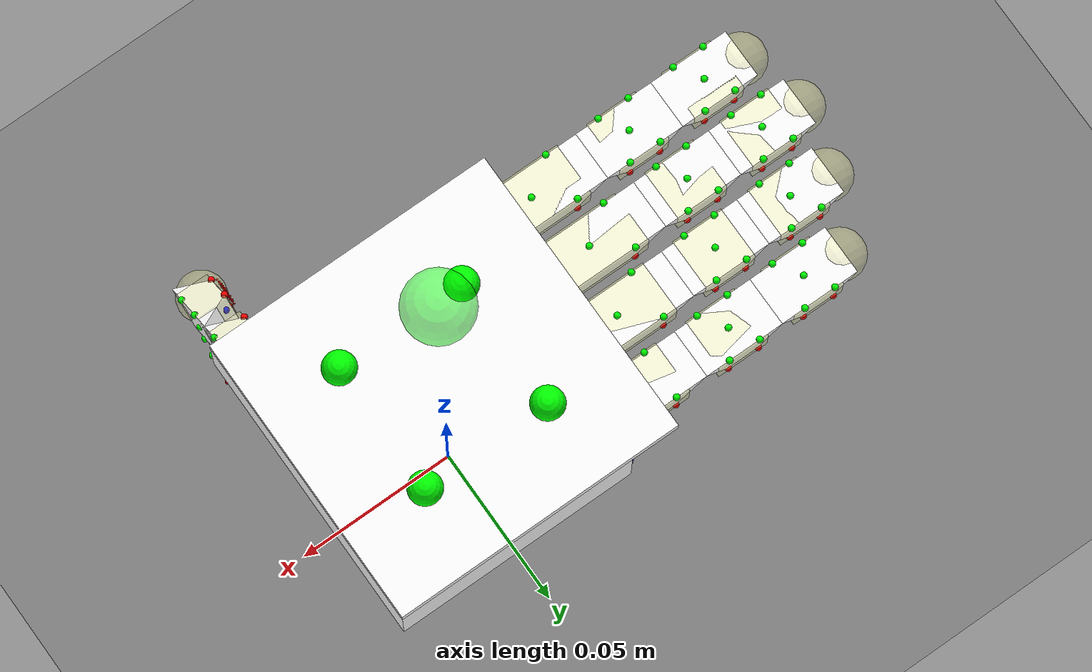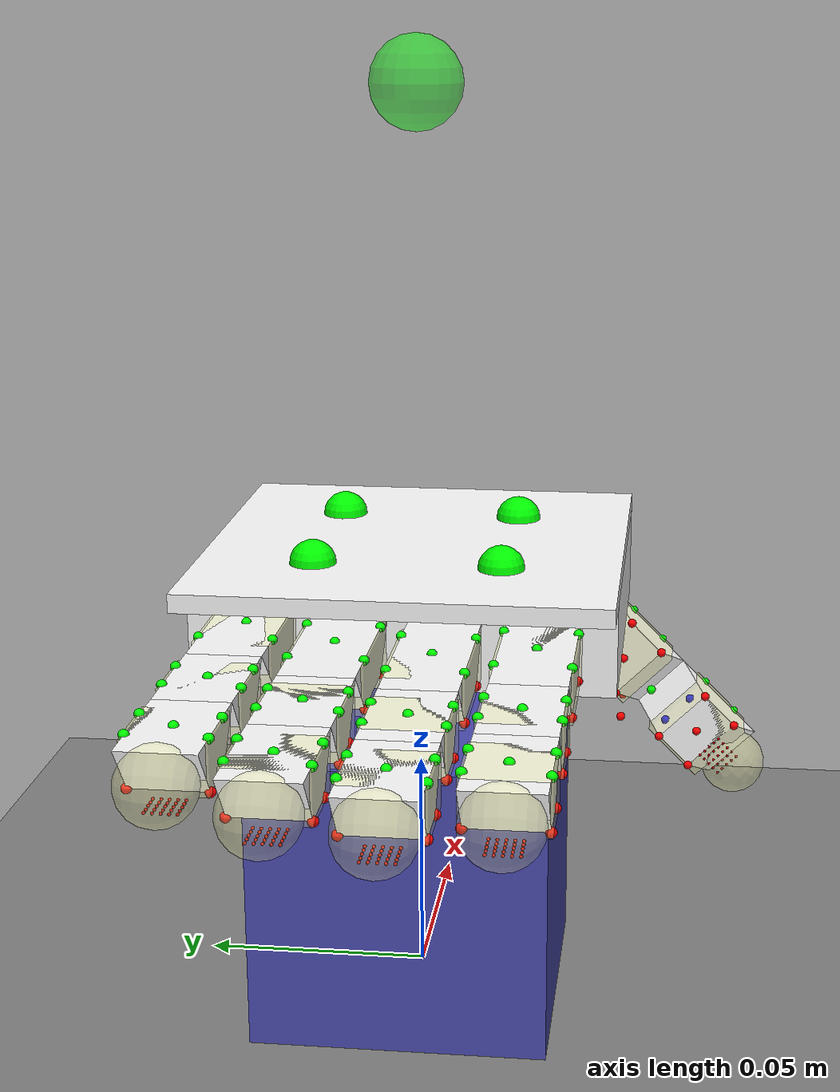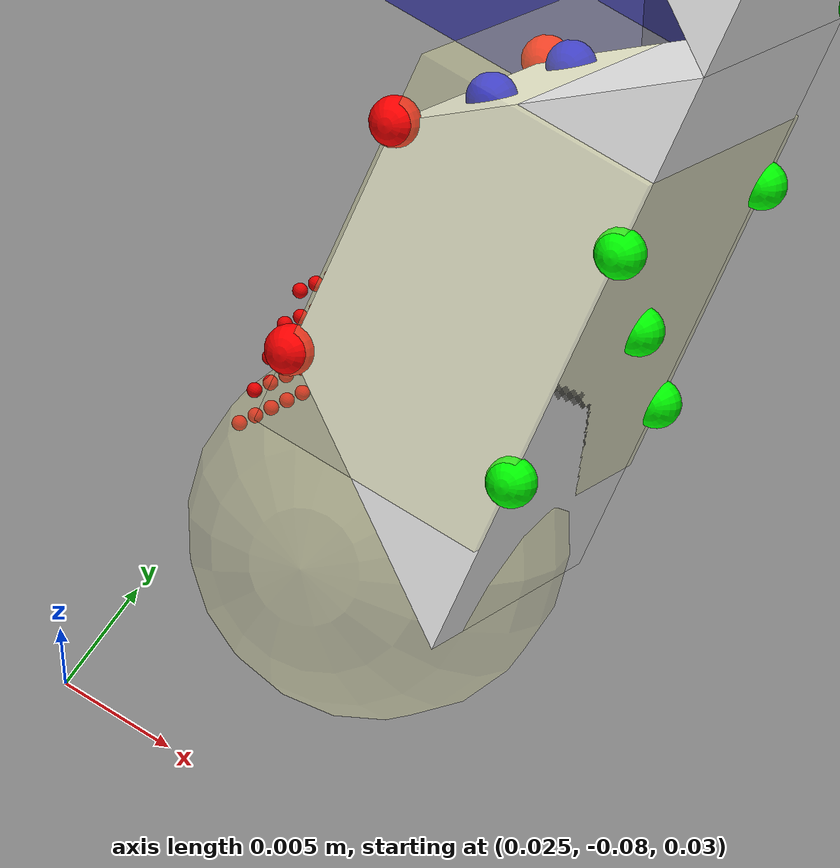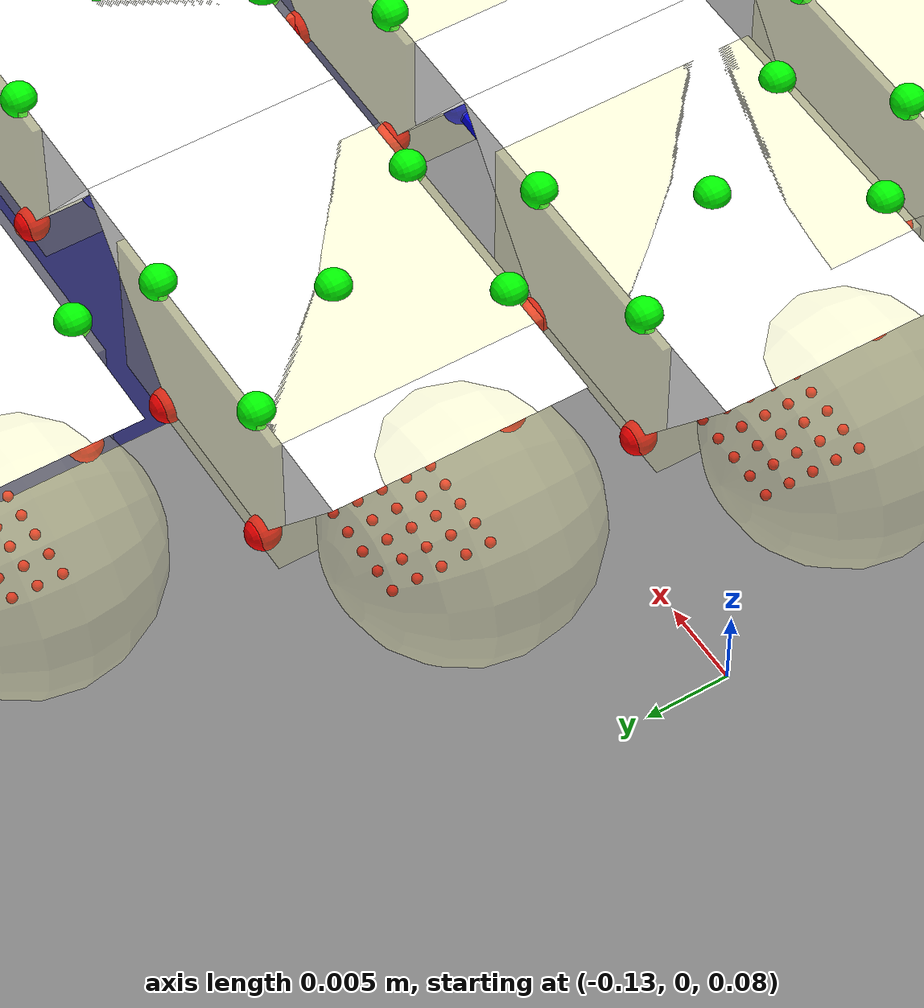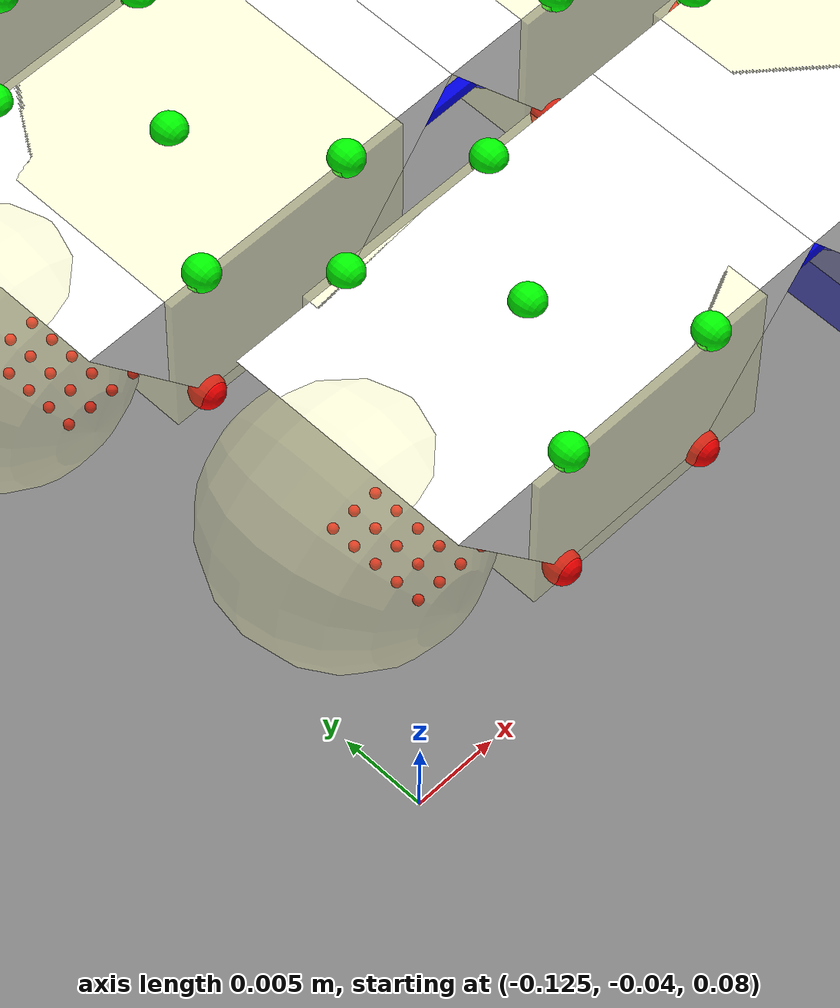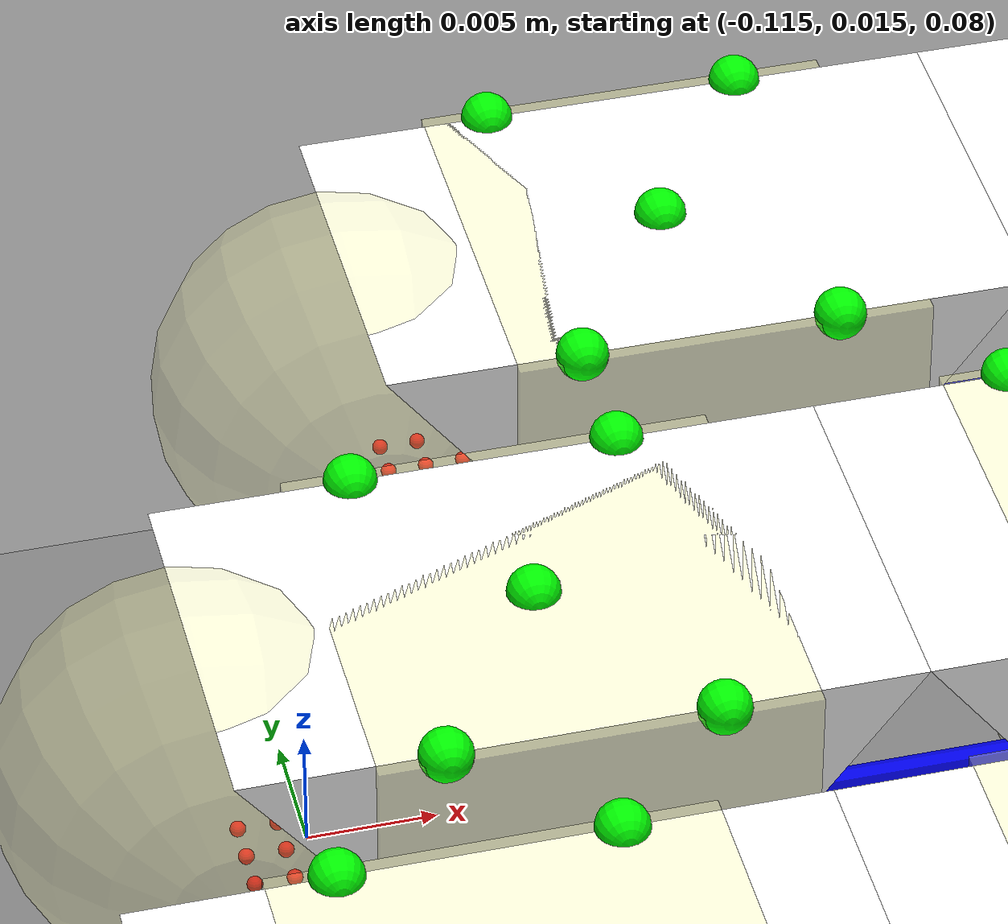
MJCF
<?xml version="1.0" ?>
<!-- Reorient手模型, 5x5 sphere tac sensors -->
<mujoco model="hand">
    <compiler angle="radian"/>
    <option integrator="implicitfast" />
    <option>
        <flag filterparent="disable"/>
    </option>
    <option gravity="0 0 -9.81"/>
    <keyframe>
        <key name="home"
            qpos="0 0 0 0 0 0 0 0 0 0 0 0 0 0 0 0 0 0 0 0 0 0 0 0 0 0 0 0 0 0 0 0"
            qvel="0 0 0 0 0 0 0 0 0 0 0 0 0 0 0 0 0 0 0 0 0 0 0 0 0 0 0 0 0 0 0"
            ctrl="0 0 0 0 0 0 0 0 0 0 0 0 0 0 0 0 0 0"
        />
    </keyframe>
    <default>
        <geom solref="0.001 1" solimp="0.99 0.999 0.0001"/>
        <default class="cube">
            <geom friction="2.0 0.1 0.002" contype="2" conaffinity="1" condim="4" />
        </default>
        <default class="hand">
            <geom contype="1" conaffinity="2" type="mesh" density="1250" friction="0.7 0.05 0.0002" solref="0.02 1.5" solimp="0.9 0.95 0.001" condim="3" rgba="0 0 1 0"/>
        </default>
        <default class="visual">
            <geom contype="0" conaffinity="0" group="2" density="0"/>
        </default>
        <default class="tendon">
            <tendon width=".0005" rgba="0 0 .9 1" solreflimit=".001 1" solimplimit="0.99 0.999 0.00001 0.1 20" stiffness="2000"/>
        </default>
        <default class="thumb_joint">
            <joint type="hinge" limited="true" solreflimit=".001 1" solimplimit="0.97 0.99 0.00001 0.1 2" damping="1" stiffness="1"/>
        </default>
        <default class="tip">
            <geom type="sphere" size="0.0075" rgba="1 1 .6 .3" contype="1" conaffinity="2" density="1000"
            friction="2.5 0.2 0.01" solref="0.01 1" solimp="0.98 0.995 0.001" condim="6"/>
        </default>
    </default>
    <asset>
        <mesh name="thumb_base_link" vertex="0.0 0.0 -0.0075 0.04 0.0 -0.0075 0.03 0.01 -0.0075 0.01 0.01 -0.0075 0.0 0.0 0.0075 0.04 0.0 0.0075 0.03 0.01 0.0075 0.01 0.01 0.0075" normal="-0.7734590803390136 -0.3203772410170408 -0.5469181606780271 0.7734590803390136 -0.3203772410170408 -0.5469181606780271 0.2971085791188998 0.7172835612062476 -0.6302624731310217 -0.2971085791188997 0.7172835612062475 -0.6302624731310217 -0.7734590803390136 -0.32037724101704074 0.5469181606780271 0.7734590803390138 -0.32037724101704057 0.5469181606780271 0.29710857911889976 0.7172835612062477 0.6302624731310216 -0.29710857911889976 0.7172835612062476 0.6302624731310217" face="1 0 3 3 2 1 7 4 5 5 6 7 5 4 1 1 4 0 6 5 2 2 5 1 4 7 0 0 7 3 7 6 3 3 6 2"/>
        <mesh name="thumb_link_1" vertex="0.0 0.0 -0.0075 0.04 0.0 -0.0075 0.03 0.01 -0.0075 0.01 0.01 -0.0075 0.0 0.0 0.0075 0.04 0.0 0.0075 0.03 0.01 0.0075 0.01 0.01 0.0075" normal="-0.7734590803390136 -0.3203772410170408 -0.5469181606780271 0.7734590803390136 -0.3203772410170408 -0.5469181606780271 0.2971085791188998 0.7172835612062476 -0.6302624731310217 -0.2971085791188997 0.7172835612062475 -0.6302624731310217 -0.7734590803390136 -0.32037724101704074 0.5469181606780271 0.7734590803390138 -0.32037724101704057 0.5469181606780271 0.29710857911889976 0.7172835612062477 0.6302624731310216 -0.29710857911889976 0.7172835612062476 0.6302624731310217" face="1 0 3 3 2 1 7 4 5 5 6 7 5 4 1 1 4 0 6 5 2 2 5 1 4 7 0 0 7 3 7 6 3 3 6 2"/>
        <mesh name="thumb_link_2" vertex="0.0 0.0 -0.0075 0.025 0.0 -0.0075 0.0175 0.01 -0.0075 0.007500000000000001 0.01 -0.0075 0.0 0.0 0.0075 0.025 0.0 0.0075 0.0175 0.01 0.0075 0.007500000000000001 0.01 0.0075" normal="-0.7464925414001442 -0.3732462707000721 -0.5508503490444955 0.7464925414001442 -0.3732462707000721 -0.5508503490444956 0.351257248032334 0.702514496064668 -0.618944043128098 -0.351257248032334 0.702514496064668 -0.618944043128098 -0.7464925414001442 -0.3732462707000721 0.5508503490444955 0.7464925414001442 -0.373246270700072 0.5508503490444956 0.351257248032334 0.7025144960646681 0.618944043128098 -0.351257248032334 0.702514496064668 0.618944043128098" face="1 0 3 3 2 1 7 4 5 5 6 7 5 4 1 1 4 0 6 5 2 2 5 1 4 7 0 0 7 3 7 6 3 3 6 2"/>
        <mesh name="thumb_link_3" vertex="0.0 0.0 -0.0075 0.025 0.0 -0.0075 0.0175 0.01 -0.0075 0.007500000000000001 0.01 -0.0075 0.0 0.0 0.0075 0.025 0.0 0.0075 0.0175 0.01 0.0075 0.007500000000000001 0.01 0.0075" normal="-0.7464925414001442 -0.3732462707000721 -0.5508503490444955 0.7464925414001442 -0.3732462707000721 -0.5508503490444956 0.351257248032334 0.702514496064668 -0.618944043128098 -0.351257248032334 0.702514496064668 -0.618944043128098 -0.7464925414001442 -0.3732462707000721 0.5508503490444955 0.7464925414001442 -0.373246270700072 0.5508503490444956 0.351257248032334 0.7025144960646681 0.618944043128098 -0.351257248032334 0.702514496064668 0.618944043128098" face="1 0 3 3 2 1 7 4 5 5 6 7 5 4 1 1 4 0 6 5 2 2 5 1 4 7 0 0 7 3 7 6 3 3 6 2"/>
        <mesh name="index_base_link" vertex="0.0 0.0 -0.0075 0.04 0.0 -0.0075 0.03 0.01 -0.0075 0.01 0.01 -0.0075 0.0 0.0 0.0075 0.04 0.0 0.0075 0.03 0.01 0.0075 0.01 0.01 0.0075" normal="-0.7734590803390136 -0.3203772410170408 -0.5469181606780271 0.7734590803390136 -0.3203772410170408 -0.5469181606780271 0.2971085791188998 0.7172835612062476 -0.6302624731310217 -0.2971085791188997 0.7172835612062475 -0.6302624731310217 -0.7734590803390136 -0.32037724101704074 0.5469181606780271 0.7734590803390138 -0.32037724101704057 0.5469181606780271 0.29710857911889976 0.7172835612062477 0.6302624731310216 -0.29710857911889976 0.7172835612062476 0.6302624731310217" face="1 0 3 3 2 1 7 4 5 5 6 7 5 4 1 1 4 0 6 5 2 2 5 1 4 7 0 0 7 3 7 6 3 3 6 2"/>
        <mesh name="index_link_1" vertex="0.0 0.0 -0.0075 0.04 0.0 -0.0075 0.03 0.01 -0.0075 0.01 0.01 -0.0075 0.0 0.0 0.0075 0.04 0.0 0.0075 0.03 0.01 0.0075 0.01 0.01 0.0075" normal="-0.7734590803390136 -0.3203772410170408 -0.5469181606780271 0.7734590803390136 -0.3203772410170408 -0.5469181606780271 0.2971085791188998 0.7172835612062476 -0.6302624731310217 -0.2971085791188997 0.7172835612062475 -0.6302624731310217 -0.7734590803390136 -0.32037724101704074 0.5469181606780271 0.7734590803390138 -0.32037724101704057 0.5469181606780271 0.29710857911889976 0.7172835612062477 0.6302624731310216 -0.29710857911889976 0.7172835612062476 0.6302624731310217" face="1 0 3 3 2 1 7 4 5 5 6 7 5 4 1 1 4 0 6 5 2 2 5 1 4 7 0 0 7 3 7 6 3 3 6 2"/>
        <mesh name="index_link_2" vertex="0.0 0.0 -0.0075 0.025 0.0 -0.0075 0.0175 0.01 -0.0075 0.007500000000000001 0.01 -0.0075 0.0 0.0 0.0075 0.025 0.0 0.0075 0.0175 0.01 0.0075 0.007500000000000001 0.01 0.0075" normal="-0.7464925414001442 -0.3732462707000721 -0.5508503490444955 0.7464925414001442 -0.3732462707000721 -0.5508503490444956 0.351257248032334 0.702514496064668 -0.618944043128098 -0.351257248032334 0.702514496064668 -0.618944043128098 -0.7464925414001442 -0.3732462707000721 0.5508503490444955 0.7464925414001442 -0.373246270700072 0.5508503490444956 0.351257248032334 0.7025144960646681 0.618944043128098 -0.351257248032334 0.702514496064668 0.618944043128098" face="1 0 3 3 2 1 7 4 5 5 6 7 5 4 1 1 4 0 6 5 2 2 5 1 4 7 0 0 7 3 7 6 3 3 6 2"/>
        <mesh name="index_link_3" vertex="0.0 0.0 -0.0075 0.025 0.0 -0.0075 0.0175 0.01 -0.0075 0.007500000000000001 0.01 -0.0075 0.0 0.0 0.0075 0.025 0.0 0.0075 0.0175 0.01 0.0075 0.007500000000000001 0.01 0.0075" normal="-0.7464925414001442 -0.3732462707000721 -0.5508503490444955 0.7464925414001442 -0.3732462707000721 -0.5508503490444956 0.351257248032334 0.702514496064668 -0.618944043128098 -0.351257248032334 0.702514496064668 -0.618944043128098 -0.7464925414001442 -0.3732462707000721 0.5508503490444955 0.7464925414001442 -0.373246270700072 0.5508503490444956 0.351257248032334 0.7025144960646681 0.618944043128098 -0.351257248032334 0.702514496064668 0.618944043128098" face="1 0 3 3 2 1 7 4 5 5 6 7 5 4 1 1 4 0 6 5 2 2 5 1 4 7 0 0 7 3 7 6 3 3 6 2"/>
        <mesh name="middle_base_link" vertex="0.0 0.0 -0.0075 0.04 0.0 -0.0075 0.03 0.01 -0.0075 0.01 0.01 -0.0075 0.0 0.0 0.0075 0.04 0.0 0.0075 0.03 0.01 0.0075 0.01 0.01 0.0075" normal="-0.7734590803390136 -0.3203772410170408 -0.5469181606780271 0.7734590803390136 -0.3203772410170408 -0.5469181606780271 0.2971085791188998 0.7172835612062476 -0.6302624731310217 -0.2971085791188997 0.7172835612062475 -0.6302624731310217 -0.7734590803390136 -0.32037724101704074 0.5469181606780271 0.7734590803390138 -0.32037724101704057 0.5469181606780271 0.29710857911889976 0.7172835612062477 0.6302624731310216 -0.29710857911889976 0.7172835612062476 0.6302624731310217" face="1 0 3 3 2 1 7 4 5 5 6 7 5 4 1 1 4 0 6 5 2 2 5 1 4 7 0 0 7 3 7 6 3 3 6 2"/>
        <mesh name="middle_link_1" vertex="0.0 0.0 -0.0075 0.04 0.0 -0.0075 0.03 0.01 -0.0075 0.01 0.01 -0.0075 0.0 0.0 0.0075 0.04 0.0 0.0075 0.03 0.01 0.0075 0.01 0.01 0.0075" normal="-0.7734590803390136 -0.3203772410170408 -0.5469181606780271 0.7734590803390136 -0.3203772410170408 -0.5469181606780271 0.2971085791188998 0.7172835612062476 -0.6302624731310217 -0.2971085791188997 0.7172835612062475 -0.6302624731310217 -0.7734590803390136 -0.32037724101704074 0.5469181606780271 0.7734590803390138 -0.32037724101704057 0.5469181606780271 0.29710857911889976 0.7172835612062477 0.6302624731310216 -0.29710857911889976 0.7172835612062476 0.6302624731310217" face="1 0 3 3 2 1 7 4 5 5 6 7 5 4 1 1 4 0 6 5 2 2 5 1 4 7 0 0 7 3 7 6 3 3 6 2"/>
        <mesh name="middle_link_2" vertex="0.0 0.0 -0.0075 0.025 0.0 -0.0075 0.0175 0.01 -0.0075 0.007500000000000001 0.01 -0.0075 0.0 0.0 0.0075 0.025 0.0 0.0075 0.0175 0.01 0.0075 0.007500000000000001 0.01 0.0075" normal="-0.7464925414001442 -0.3732462707000721 -0.5508503490444955 0.7464925414001442 -0.3732462707000721 -0.5508503490444956 0.351257248032334 0.702514496064668 -0.618944043128098 -0.351257248032334 0.702514496064668 -0.618944043128098 -0.7464925414001442 -0.3732462707000721 0.5508503490444955 0.7464925414001442 -0.373246270700072 0.5508503490444956 0.351257248032334 0.7025144960646681 0.618944043128098 -0.351257248032334 0.702514496064668 0.618944043128098" face="1 0 3 3 2 1 7 4 5 5 6 7 5 4 1 1 4 0 6 5 2 2 5 1 4 7 0 0 7 3 7 6 3 3 6 2"/>
        <mesh name="middle_link_3" vertex="0.0 0.0 -0.0075 0.025 0.0 -0.0075 0.0175 0.01 -0.0075 0.007500000000000001 0.01 -0.0075 0.0 0.0 0.0075 0.025 0.0 0.0075 0.0175 0.01 0.0075 0.007500000000000001 0.01 0.0075" normal="-0.7464925414001442 -0.3732462707000721 -0.5508503490444955 0.7464925414001442 -0.3732462707000721 -0.5508503490444956 0.351257248032334 0.702514496064668 -0.618944043128098 -0.351257248032334 0.702514496064668 -0.618944043128098 -0.7464925414001442 -0.3732462707000721 0.5508503490444955 0.7464925414001442 -0.373246270700072 0.5508503490444956 0.351257248032334 0.7025144960646681 0.618944043128098 -0.351257248032334 0.702514496064668 0.618944043128098" face="1 0 3 3 2 1 7 4 5 5 6 7 5 4 1 1 4 0 6 5 2 2 5 1 4 7 0 0 7 3 7 6 3 3 6 2"/>
        <mesh name="ring_base_link" vertex="0.0 0.0 -0.0075 0.04 0.0 -0.0075 0.03 0.01 -0.0075 0.01 0.01 -0.0075 0.0 0.0 0.0075 0.04 0.0 0.0075 0.03 0.01 0.0075 0.01 0.01 0.0075" normal="-0.7734590803390136 -0.3203772410170408 -0.5469181606780271 0.7734590803390136 -0.3203772410170408 -0.5469181606780271 0.2971085791188998 0.7172835612062476 -0.6302624731310217 -0.2971085791188997 0.7172835612062475 -0.6302624731310217 -0.7734590803390136 -0.32037724101704074 0.5469181606780271 0.7734590803390138 -0.32037724101704057 0.5469181606780271 0.29710857911889976 0.7172835612062477 0.6302624731310216 -0.29710857911889976 0.7172835612062476 0.6302624731310217" face="1 0 3 3 2 1 7 4 5 5 6 7 5 4 1 1 4 0 6 5 2 2 5 1 4 7 0 0 7 3 7 6 3 3 6 2"/>
        <mesh name="ring_link_1" vertex="0.0 0.0 -0.0075 0.04 0.0 -0.0075 0.03 0.01 -0.0075 0.01 0.01 -0.0075 0.0 0.0 0.0075 0.04 0.0 0.0075 0.03 0.01 0.0075 0.01 0.01 0.0075" normal="-0.7734590803390136 -0.3203772410170408 -0.5469181606780271 0.7734590803390136 -0.3203772410170408 -0.5469181606780271 0.2971085791188998 0.7172835612062476 -0.6302624731310217 -0.2971085791188997 0.7172835612062475 -0.6302624731310217 -0.7734590803390136 -0.32037724101704074 0.5469181606780271 0.7734590803390138 -0.32037724101704057 0.5469181606780271 0.29710857911889976 0.7172835612062477 0.6302624731310216 -0.29710857911889976 0.7172835612062476 0.6302624731310217" face="1 0 3 3 2 1 7 4 5 5 6 7 5 4 1 1 4 0 6 5 2 2 5 1 4 7 0 0 7 3 7 6 3 3 6 2"/>
        <mesh name="ring_link_2" vertex="0.0 0.0 -0.0075 0.025 0.0 -0.0075 0.0175 0.01 -0.0075 0.007500000000000001 0.01 -0.0075 0.0 0.0 0.0075 0.025 0.0 0.0075 0.0175 0.01 0.0075 0.007500000000000001 0.01 0.0075" normal="-0.7464925414001442 -0.3732462707000721 -0.5508503490444955 0.7464925414001442 -0.3732462707000721 -0.5508503490444956 0.351257248032334 0.702514496064668 -0.618944043128098 -0.351257248032334 0.702514496064668 -0.618944043128098 -0.7464925414001442 -0.3732462707000721 0.5508503490444955 0.7464925414001442 -0.373246270700072 0.5508503490444956 0.351257248032334 0.7025144960646681 0.618944043128098 -0.351257248032334 0.702514496064668 0.618944043128098" face="1 0 3 3 2 1 7 4 5 5 6 7 5 4 1 1 4 0 6 5 2 2 5 1 4 7 0 0 7 3 7 6 3 3 6 2"/>
        <mesh name="ring_link_3" vertex="0.0 0.0 -0.0075 0.025 0.0 -0.0075 0.0175 0.01 -0.0075 0.007500000000000001 0.01 -0.0075 0.0 0.0 0.0075 0.025 0.0 0.0075 0.0175 0.01 0.0075 0.007500000000000001 0.01 0.0075" normal="-0.7464925414001442 -0.3732462707000721 -0.5508503490444955 0.7464925414001442 -0.3732462707000721 -0.5508503490444956 0.351257248032334 0.702514496064668 -0.618944043128098 -0.351257248032334 0.702514496064668 -0.618944043128098 -0.7464925414001442 -0.3732462707000721 0.5508503490444955 0.7464925414001442 -0.373246270700072 0.5508503490444956 0.351257248032334 0.7025144960646681 0.618944043128098 -0.351257248032334 0.702514496064668 0.618944043128098" face="1 0 3 3 2 1 7 4 5 5 6 7 5 4 1 1 4 0 6 5 2 2 5 1 4 7 0 0 7 3 7 6 3 3 6 2"/>
        <mesh name="little_base_link" vertex="0.0 0.0 -0.0075 0.04 0.0 -0.0075 0.03 0.01 -0.0075 0.01 0.01 -0.0075 0.0 0.0 0.0075 0.04 0.0 0.0075 0.03 0.01 0.0075 0.01 0.01 0.0075" normal="-0.7734590803390136 -0.3203772410170408 -0.5469181606780271 0.7734590803390136 -0.3203772410170408 -0.5469181606780271 0.2971085791188998 0.7172835612062476 -0.6302624731310217 -0.2971085791188997 0.7172835612062475 -0.6302624731310217 -0.7734590803390136 -0.32037724101704074 0.5469181606780271 0.7734590803390138 -0.32037724101704057 0.5469181606780271 0.29710857911889976 0.7172835612062477 0.6302624731310216 -0.29710857911889976 0.7172835612062476 0.6302624731310217" face="1 0 3 3 2 1 7 4 5 5 6 7 5 4 1 1 4 0 6 5 2 2 5 1 4 7 0 0 7 3 7 6 3 3 6 2"/>
        <mesh name="little_link_1" vertex="0.0 0.0 -0.0075 0.04 0.0 -0.0075 0.03 0.01 -0.0075 0.01 0.01 -0.0075 0.0 0.0 0.0075 0.04 0.0 0.0075 0.03 0.01 0.0075 0.01 0.01 0.0075" normal="-0.7734590803390136 -0.3203772410170408 -0.5469181606780271 0.7734590803390136 -0.3203772410170408 -0.5469181606780271 0.2971085791188998 0.7172835612062476 -0.6302624731310217 -0.2971085791188997 0.7172835612062475 -0.6302624731310217 -0.7734590803390136 -0.32037724101704074 0.5469181606780271 0.7734590803390138 -0.32037724101704057 0.5469181606780271 0.29710857911889976 0.7172835612062477 0.6302624731310216 -0.29710857911889976 0.7172835612062476 0.6302624731310217" face="1 0 3 3 2 1 7 4 5 5 6 7 5 4 1 1 4 0 6 5 2 2 5 1 4 7 0 0 7 3 7 6 3 3 6 2"/>
        <mesh name="little_link_2" vertex="0.0 0.0 -0.0075 0.025 0.0 -0.0075 0.0175 0.01 -0.0075 0.007500000000000001 0.01 -0.0075 0.0 0.0 0.0075 0.025 0.0 0.0075 0.0175 0.01 0.0075 0.007500000000000001 0.01 0.0075" normal="-0.7464925414001442 -0.3732462707000721 -0.5508503490444955 0.7464925414001442 -0.3732462707000721 -0.5508503490444956 0.351257248032334 0.702514496064668 -0.618944043128098 -0.351257248032334 0.702514496064668 -0.618944043128098 -0.7464925414001442 -0.3732462707000721 0.5508503490444955 0.7464925414001442 -0.373246270700072 0.5508503490444956 0.351257248032334 0.7025144960646681 0.618944043128098 -0.351257248032334 0.702514496064668 0.618944043128098" face="1 0 3 3 2 1 7 4 5 5 6 7 5 4 1 1 4 0 6 5 2 2 5 1 4 7 0 0 7 3 7 6 3 3 6 2"/>
        <mesh name="little_link_3" vertex="0.0 0.0 -0.0075 0.025 0.0 -0.0075 0.0175 0.01 -0.0075 0.007500000000000001 0.01 -0.0075 0.0 0.0 0.0075 0.025 0.0 0.0075 0.0175 0.01 0.0075 0.007500000000000001 0.01 0.0075" normal="-0.7464925414001442 -0.3732462707000721 -0.5508503490444955 0.7464925414001442 -0.3732462707000721 -0.5508503490444956 0.351257248032334 0.702514496064668 -0.618944043128098 -0.351257248032334 0.702514496064668 -0.618944043128098 -0.7464925414001442 -0.3732462707000721 0.5508503490444955 0.7464925414001442 -0.373246270700072 0.5508503490444956 0.351257248032334 0.7025144960646681 0.618944043128098 -0.351257248032334 0.702514496064668 0.618944043128098" face="1 0 3 3 2 1 7 4 5 5 6 7 5 4 1 1 4 0 6 5 2 2 5 1 4 7 0 0 7 3 7 6 3 3 6 2"/>
        <texture type="2d" name="groundplane" builtin="checker" mark="edge" rgb1="1 1 1" rgb2="0 0 0" markrgb="0 0 0" width="300" height="300"/>
        <material name="groundplane" texture="groundplane" texuniform="true" texrepeat="5 5" reflectance="0"/>
    </asset>
    <worldbody>
        <!-- 一些辅助元素 -->
        <site name="target" pos="0 0 0.2" size="0.01" rgba="0 1 0 0.5"/>
        <geom name="floor" pos="0 0 0" size="0 0 0.01" type="plane" material="groundplane" contype="1" conaffinity="1" friction="1 0.05 0.05" solref="0.001 1" solimp="0.98 0.99 0.001"/>
        <!-- 手的定义 -->
        <body name="palm" pos="0 0 0.1" euler="0 3.1415 0" childclass="hand">
            <joint name="palm_slide_x" type="slide" axis="1 0 0" range="-.5 .5" limited="true" solreflimit=".001 1" solimplimit="0.97 0.99 0.00001 0.1 2" damping="0.2"/>
            <joint name="palm_slide_y" type="slide" axis="0 1 0" range="-.5 .5" limited="true" solreflimit=".001 1" solimplimit="0.97 0.99 0.00001 0.1 2" damping="0.2"/>
            <joint name="palm_slide_z" type="slide" axis="0 0 1" range="-.2 .12" limited="true" solreflimit=".001 1" solimplimit="0.97 0.99 0.00001 0.1 2" damping="0.2"/>
            <joint name="palm_rotate_x" type="hinge" axis="1 0 0" range="-1.57 1.57" limited="true" solreflimit=".001 1" solimplimit="0.97 0.99 0.00001 0.1 2" damping="0.2"/>
            <joint name="palm_rotate_y" type="hinge" axis="0 1 0" range="-1.57 1.57" limited="true" solreflimit=".001 1" solimplimit="0.97 0.99 0.00001 0.1 2" damping="0.2"/>
            <joint name="palm_rotate_z" type="hinge" axis="0 0 1" range="-3.14 3.14" limited="true" solreflimit=".001 1" solimplimit="0.97 0.99 0.00001 0.1 2" damping="0.2"/>
            <geom type="box" size="0.045 0.045 0.002" rgba="1 1 1 1" density="200"/>
            <geom type="box" size="0.0375 0.045 0.01" pos="-0.0075 0 0.012" rgba="1 1 1 1" density="200"/>
            <site name="inner_palm_1" size="0.005" rgba="1 0 0 1" pos=".02 .02 0.022"/>
            <site name="inner_palm_2" size="0.005" rgba="1 0 0 1" pos=".02 -.02 0.022"/>
            <site name="inner_palm_3" size="0.005" rgba="1 0 0 1" pos="-.02 .02 0.022"/>
            <site name="inner_palm_4" size="0.005" rgba="1 0 0 1" pos="-.02 -.02 0.022"/>
            <site name="outer_palm_1" size="0.005" rgba="0 1 0 1" pos=".02 .02 -0.002"/>
            <site name="outer_palm_2" size="0.005" rgba="0 1 0 1" pos=".02 -.02 -0.002"/>
            <site name="outer_palm_3" size="0.005" rgba="0 1 0 1" pos="-.02 .02 -0.002"/>
            <site name="outer_palm_4" size="0.005" rgba="0 1 0 1" pos="-.02 -.02 -0.002"/>
            <!-- 拇指基座 -->
            <body name="thumb_base_link" pos="-0.035 -0.02 0.01" euler="1.57 -1.57 0.0">
                <joint name="thumb_joint_0" axis="0 1 0" range="-0.5 0.5" class="thumb_joint"/>
                <inertial pos="0 0 0" mass="0.01" diaginertia="1e-5 1e-5 1e-5"/>
                <geom type="sphere" size=".002" class="visual"/>
                <!-- 拇指第一节 -->
                <body name="thumb_link_1" pos="0.01 0.01 0.0" euler="0.0 0.0 0.785">
                    <joint name="thumb_joint_1" axis="0 0 1" range="0 2.8" class="thumb_joint"/>
                    <geom class="visual" type="sphere" size=".002"/>
                    <inertial pos="0 0 0" mass="0.01" diaginertia="1e-5 1e-5 1e-5"/>
                    <geom type="box" size="0.007 0.005 0.005" rgba="0 1 0 0.3" density="200" class="visual"/>
                    <site name="inner_thumb_1_0" size="0.001" rgba="1 0 0 1" pos="0.02 0.01 0"/>
                    <site name="inner_thumb_1_1" size="0.001" rgba="1 0 0 1" pos="0.01 0.01 0.0075"/>
                    <site name="inner_thumb_1_2" size="0.001" rgba="1 0 0 1" pos="0.01 0.01 -0.0075"/>
                    <site name="inner_thumb_1_3" size="0.001" rgba="1 0 0 1" pos="0.03 0.01 0.0075"/>
                    <site name="inner_thumb_1_4" size="0.001" rgba="1 0 0 1" pos="0.03 0.01 -0.0075"/>
                    <site name="outer_thumb_1_0" size="0.001" rgba="0 1 0 1" pos="0.02 0 0"/>
                    <site name="outer_thumb_1_1" size="0.001" rgba="0 1 0 1" pos="0.01 0 0.0075"/>
                    <site name="outer_thumb_1_2" size="0.001" rgba="0 1 0 1" pos="0.01 0 -0.0075"/>
                    <site name="outer_thumb_1_3" size="0.001" rgba="0 1 0 1" pos="0.03 0 0.0075"/>
                    <site name="outer_thumb_1_4" size="0.001" rgba="0 1 0 1" pos="0.03 0 -0.0075"/>
                    <!-- 拇指第二节 -->
                    <body name="thumb_link_2" pos="0.008 0 0.005" euler="-1.57 0 0">
                        <joint name="thumb_joint_2" axis="0 0 1" range="0 0.5" class="thumb_joint"/>
                        <geom class="visual" type="mesh" rgba="1 1 1 1" mesh="thumb_link_2"/>
                        <geom type="mesh" mesh="thumb_link_2" rgba="0 0 1 1" density="200" class="visual"/>
                        <geom name="thumb_link_2_collision_box" type="box" pos="0.0125 0.005 0" size="0.008 0.005 0.008" rgba="1 1 .6 .3" />
                        <site name="inner_thumb_2_0" size="0.001" rgba="1 0 0 1" pos="0.0125 0.01 0"/>
                        <site name="inner_thumb_2_1" size="0.001" rgba="1 0 0 1" pos="0.007500000000000001 0.01 0.0075"/>
                        <site name="inner_thumb_2_2" size="0.001" rgba="1 0 0 1" pos="0.007500000000000001 0.01 -0.0075"/>
                        <site name="inner_thumb_2_3" size="0.001" rgba="1 0 0 1" pos="0.0175 0.01 0.0075"/>
                        <site name="inner_thumb_2_4" size="0.001" rgba="1 0 0 1" pos="0.0175 0.01 -0.0075"/>
                        <site name="outer_thumb_2_0" size="0.001" rgba="0 1 0 1" pos="0.0125 0 0"/>
                        <site name="outer_thumb_2_1" size="0.001" rgba="0 1 0 1" pos="0.007500000000000001 0 0.0075"/>
                        <site name="outer_thumb_2_2" size="0.001" rgba="0 1 0 1" pos="0.007500000000000001 0 -0.0075"/>
                        <site name="outer_thumb_2_3" size="0.001" rgba="0 1 0 1" pos="0.0175 0 0.0075"/>
                        <site name="outer_thumb_2_4" size="0.001" rgba="0 1 0 1" pos="0.0175 0 -0.0075"/>
                        <!-- 拇指第三节 -->
                        <body name="thumb_link_3" pos="0.025 0 0" euler="0 0 0">
                            <joint name="thumb_joint_3" axis="0 0 1" range="0 0.5" class="thumb_joint"/>
                            <geom conaffinity="0" contype="0" type="mesh" rgba="1 1 1 1" mesh="thumb_link_3"/>
                            <geom type="mesh" mesh="thumb_link_3" rgba="1 1 0 1" density="200" class="visual"/>
                            <site name="thumb_t1_3" pos="0.006 0.008 0.004" size="0.001" rgba="0 0 0.9 1"/>
                            <site name="thumb_t2_3" pos="0.006 0.008 -0.004" size="0.001" rgba="0 0 0.9 1"/>
                            <geom name="thumb_link_3_collision_box" type="box" pos="0.0125 0.005 0" size="0.008 0.005 0.008" rgba="1 1 .6 .3" />
                            <geom name="thumb_tip_collision" type="sphere" pos="0.025 0.006 0" class="tip"/>
                            <site name="inner_thumb_3_0" size="0.001" rgba="1 0 0 1" pos="0.0125 0.01 0"/>
                            <site name="inner_thumb_3_1" size="0.001" rgba="1 0 0 1" pos="0.007500000000000001 0.01 0.0075"/>
                            <site name="inner_thumb_3_2" size="0.001" rgba="1 0 0 1" pos="0.007500000000000001 0.01 -0.0075"/>
                            <site name="inner_thumb_3_3" size="0.001" rgba="1 0 0 1" pos="0.0175 0.01 0.0075"/>
                            <site name="inner_thumb_3_4" size="0.001" rgba="1 0 0 1" pos="0.0175 0.01 -0.0075"/>
                            <site name="outer_thumb_3_0" size="0.001" rgba="0 1 0 1" pos="0.0125 0 0"/>
                            <site name="outer_thumb_3_1" size="0.001" rgba="0 1 0 1" pos="0.007500000000000001 0 0.0075"/>
                            <site name="outer_thumb_3_2" size="0.001" rgba="0 1 0 1" pos="0.007500000000000001 0 -0.0075"/>
                            <site name="outer_thumb_3_3" size="0.001" rgba="0 1 0 1" pos="0.0175 0 0.0075"/>
                            <site name="outer_thumb_3_4" size="0.001" rgba="0 1 0 1" pos="0.0175 0 -0.0075"/>
                            <body name="thumb_fingertip" pos="0.02 0.01 0" euler="1.57 0 0">
                                <geom type="sphere" pos="0 0 0" size=".001" rgba=".9 0 0 .1"/>
                                <body name="thumb_markerB_0_0" pos="-0.003 -0.003 -0.002">
                                    <geom name="thumb_markerG_0_0" type="sphere"  rgba=".9 0 0 .9" size="0.0003" mass=".0001" friction="0.7 0.05 0.0002" solref="0.02 1.5" solimp="0.9 0.99 0.001" condim="3"/>
                                </body>
                                <body name="thumb_markerB_0_1" pos="-0.003 -0.0015 -0.002">
                                    <geom name="thumb_markerG_0_1" type="sphere"  rgba=".9 0 0 .9" size="0.0003" mass=".0001" friction="0.7 0.05 0.0002" solref="0.02 1.5" solimp="0.9 0.99 0.001" condim="3"/>
                                </body>
                                <body name="thumb_markerB_0_2" pos="-0.003 0.0 -0.002">
                                    <geom name="thumb_markerG_0_2" type="sphere"  rgba=".9 0 0 .9" size="0.0003" mass=".0001" friction="0.7 0.05 0.0002" solref="0.02 1.5" solimp="0.9 0.99 0.001" condim="3"/>
                                </body>
                                <body name="thumb_markerB_0_3" pos="-0.003 0.0015000000000000005 -0.002">
                                    <geom name="thumb_markerG_0_3" type="sphere"  rgba=".9 0 0 .9" size="0.0003" mass=".0001" friction="0.7 0.05 0.0002" solref="0.02 1.5" solimp="0.9 0.99 0.001" condim="3"/>
                                </body>
                                <body name="thumb_markerB_0_4" pos="-0.003 0.003 -0.002">
                                    <geom name="thumb_markerG_0_4" type="sphere"  rgba=".9 0 0 .9" size="0.0003" mass=".0001" friction="0.7 0.05 0.0002" solref="0.02 1.5" solimp="0.9 0.99 0.001" condim="3"/>
                                </body>
                                <body name="thumb_markerB_1_0" pos="-0.0015 -0.003 -0.002">
                                    <geom name="thumb_markerG_1_0" type="sphere"  rgba=".9 0 0 .9" size="0.0003" mass=".0001" friction="0.7 0.05 0.0002" solref="0.02 1.5" solimp="0.9 0.99 0.001" condim="3"/>
                                </body>
                                <body name="thumb_markerB_1_1" pos="-0.0015 -0.0015 -0.002">
                                    <geom name="thumb_markerG_1_1" type="sphere"  rgba=".9 0 0 .9" size="0.0003" mass=".0001" friction="0.7 0.05 0.0002" solref="0.02 1.5" solimp="0.9 0.99 0.001" condim="3"/>
                                </body>
                                <body name="thumb_markerB_1_2" pos="-0.0015 0.0 -0.002">
                                    <geom name="thumb_markerG_1_2" type="sphere"  rgba=".9 0 0 .9" size="0.0003" mass=".0001" friction="0.7 0.05 0.0002" solref="0.02 1.5" solimp="0.9 0.99 0.001" condim="3"/>
                                </body>
                                <body name="thumb_markerB_1_3" pos="-0.0015 0.0015000000000000005 -0.002">
                                    <geom name="thumb_markerG_1_3" type="sphere"  rgba=".9 0 0 .9" size="0.0003" mass=".0001" friction="0.7 0.05 0.0002" solref="0.02 1.5" solimp="0.9 0.99 0.001" condim="3"/>
                                </body>
                                <body name="thumb_markerB_1_4" pos="-0.0015 0.003 -0.002">
                                    <geom name="thumb_markerG_1_4" type="sphere"  rgba=".9 0 0 .9" size="0.0003" mass=".0001" friction="0.7 0.05 0.0002" solref="0.02 1.5" solimp="0.9 0.99 0.001" condim="3"/>
                                </body>
                                <body name="thumb_markerB_2_0" pos="0.0 -0.003 -0.002">
                                    <geom name="thumb_markerG_2_0" type="sphere"  rgba=".9 0 0 .9" size="0.0003" mass=".0001" friction="0.7 0.05 0.0002" solref="0.02 1.5" solimp="0.9 0.99 0.001" condim="3"/>
                                </body>
                                <body name="thumb_markerB_2_1" pos="0.0 -0.0015 -0.002">
                                    <geom name="thumb_markerG_2_1" type="sphere"  rgba=".9 0 0 .9" size="0.0003" mass=".0001" friction="0.7 0.05 0.0002" solref="0.02 1.5" solimp="0.9 0.99 0.001" condim="3"/>
                                </body>
                                <body name="thumb_markerB_2_2" pos="0.0 0.0 -0.002">
                                    <geom name="thumb_markerG_2_2" type="sphere"  rgba=".9 0 0 .9" size="0.0003" mass=".0001" friction="0.7 0.05 0.0002" solref="0.02 1.5" solimp="0.9 0.99 0.001" condim="3"/>
                                </body>
                                <body name="thumb_markerB_2_3" pos="0.0 0.0015000000000000005 -0.002">
                                    <geom name="thumb_markerG_2_3" type="sphere"  rgba=".9 0 0 .9" size="0.0003" mass=".0001" friction="0.7 0.05 0.0002" solref="0.02 1.5" solimp="0.9 0.99 0.001" condim="3"/>
                                </body>
                                <body name="thumb_markerB_2_4" pos="0.0 0.003 -0.002">
                                    <geom name="thumb_markerG_2_4" type="sphere"  rgba=".9 0 0 .9" size="0.0003" mass=".0001" friction="0.7 0.05 0.0002" solref="0.02 1.5" solimp="0.9 0.99 0.001" condim="3"/>
                                </body>
                                <body name="thumb_markerB_3_0" pos="0.0015000000000000005 -0.003 -0.002">
                                    <geom name="thumb_markerG_3_0" type="sphere"  rgba=".9 0 0 .9" size="0.0003" mass=".0001" friction="0.7 0.05 0.0002" solref="0.02 1.5" solimp="0.9 0.99 0.001" condim="3"/>
                                </body>
                                <body name="thumb_markerB_3_1" pos="0.0015000000000000005 -0.0015 -0.002">
                                    <geom name="thumb_markerG_3_1" type="sphere"  rgba=".9 0 0 .9" size="0.0003" mass=".0001" friction="0.7 0.05 0.0002" solref="0.02 1.5" solimp="0.9 0.99 0.001" condim="3"/>
                                </body>
                                <body name="thumb_markerB_3_2" pos="0.0015000000000000005 0.0 -0.002">
                                    <geom name="thumb_markerG_3_2" type="sphere"  rgba=".9 0 0 .9" size="0.0003" mass=".0001" friction="0.7 0.05 0.0002" solref="0.02 1.5" solimp="0.9 0.99 0.001" condim="3"/>
                                </body>
                                <body name="thumb_markerB_3_3" pos="0.0015000000000000005 0.0015000000000000005 -0.002">
                                    <geom name="thumb_markerG_3_3" type="sphere"  rgba=".9 0 0 .9" size="0.0003" mass=".0001" friction="0.7 0.05 0.0002" solref="0.02 1.5" solimp="0.9 0.99 0.001" condim="3"/>
                                </body>
                                <body name="thumb_markerB_3_4" pos="0.0015000000000000005 0.003 -0.002">
                                    <geom name="thumb_markerG_3_4" type="sphere"  rgba=".9 0 0 .9" size="0.0003" mass=".0001" friction="0.7 0.05 0.0002" solref="0.02 1.5" solimp="0.9 0.99 0.001" condim="3"/>
                                </body>
                                <body name="thumb_markerB_4_0" pos="0.003 -0.003 -0.002">
                                    <geom name="thumb_markerG_4_0" type="sphere"  rgba=".9 0 0 .9" size="0.0003" mass=".0001" friction="0.7 0.05 0.0002" solref="0.02 1.5" solimp="0.9 0.99 0.001" condim="3"/>
                                </body>
                                <body name="thumb_markerB_4_1" pos="0.003 -0.0015 -0.002">
                                    <geom name="thumb_markerG_4_1" type="sphere"  rgba=".9 0 0 .9" size="0.0003" mass=".0001" friction="0.7 0.05 0.0002" solref="0.02 1.5" solimp="0.9 0.99 0.001" condim="3"/>
                                </body>
                                <body name="thumb_markerB_4_2" pos="0.003 0.0 -0.002">
                                    <geom name="thumb_markerG_4_2" type="sphere"  rgba=".9 0 0 .9" size="0.0003" mass=".0001" friction="0.7 0.05 0.0002" solref="0.02 1.5" solimp="0.9 0.99 0.001" condim="3"/>
                                </body>
                                <body name="thumb_markerB_4_3" pos="0.003 0.0015000000000000005 -0.002">
                                    <geom name="thumb_markerG_4_3" type="sphere"  rgba=".9 0 0 .9" size="0.0003" mass=".0001" friction="0.7 0.05 0.0002" solref="0.02 1.5" solimp="0.9 0.99 0.001" condim="3"/>
                                </body>
                                <body name="thumb_markerB_4_4" pos="0.003 0.003 -0.002">
                                    <geom name="thumb_markerG_4_4" type="sphere"  rgba=".9 0 0 .9" size="0.0003" mass=".0001" friction="0.7 0.05 0.0002" solref="0.02 1.5" solimp="0.9 0.99 0.001" condim="3"/>
                                </body>
                            </body>
                        </body>
                    </body>
                </body>
            </body>
            <body name="index_base_link" pos="0.015 -0.03 0.005" euler="1.57 0.0 0.0">
                <joint name="index_swing" axis="0 -1 0" range="0 0.5" damping="0.2"/>
                <geom type="sphere" size=".002"/>
                <site name="index_t12" pos="0 0 0" size="0.001" rgba="0 0 0.9 1"/>
                <site name="index_t0" pos="-0.01 0 0" size="0.001" rgba="0 0 0.9 1"/>
                <body name="index_link_1" pos="0.015 0 0">
                    <joint name="index_joint_0" pos="0 0 0" axis="0 0 1" stiffness="0.2" springref="0.0" damping="0.2" range="0 3.14" frictionloss="0.08"/>
                    <geom name="index_link_1_collision_box" type="box" pos="0.02 0.005 0" size="0.014 0.005 0.008" rgba="1 1 .6 .3" />
                    <geom type="mesh" rgba="1 1 1 1" mesh="index_link_1" class="visual"/>
                    <site name="index_t1_1_1" pos="0.008 0.008 0.004" size="0.001" rgba="0 0 0.9 1"/>
                    <site name="index_t2_1_1" pos="0.008 0.008 -0.004" size="0.001" rgba="0 0 0.9 1"/>
                    <site name="index_t1_1_2" pos="0.032 0.008 0.004" size="0.001" rgba="0 0 0.9 1"/>
                    <site name="index_t2_1_2" pos="0.032 0.008 -0.004" size="0.001" rgba="0 0 0.9 1"/>
                    <site name="inner_index_1_0" size="0.001" rgba="1 0 0 1" pos="0.02 0.01 0"/>
                    <site name="inner_index_1_1" size="0.001" rgba="1 0 0 1" pos="0.01 0.01 0.0075"/>
                    <site name="inner_index_1_2" size="0.001" rgba="1 0 0 1" pos="0.01 0.01 -0.0075"/>
                    <site name="inner_index_1_3" size="0.001" rgba="1 0 0 1" pos="0.03 0.01 0.0075"/>
                    <site name="inner_index_1_4" size="0.001" rgba="1 0 0 1" pos="0.03 0.01 -0.0075"/>
                    <site name="outer_index_1_0" size="0.001" rgba="0 1 0 1" pos="0.02 0 0"/>
                    <site name="outer_index_1_1" size="0.001" rgba="0 1 0 1" pos="0.01 0 0.0075"/>
                    <site name="outer_index_1_2" size="0.001" rgba="0 1 0 1" pos="0.01 0 -0.0075"/>
                    <site name="outer_index_1_3" size="0.001" rgba="0 1 0 1" pos="0.03 0 0.0075"/>
                    <site name="outer_index_1_4" size="0.001" rgba="0 1 0 1" pos="0.03 0 -0.0075"/>
                    <body name="index_link_2" pos="0.04 0 0">
                        <joint name="index_joint_1" pos="0 0 0" axis="0 0 1" stiffness="0.2" springref="0.0" damping="0.05" range="0 3.14" frictionloss="0.04"/>
                        <geom name="index_link_2_collision_box" type="box" pos="0.012 0.005 0" size="0.008 0.005 0.008" rgba="1 1 .6 .3" />
                        <geom type="mesh" rgba="1 1 1 1" mesh="index_link_2" class="visual"/>
                        <site name="index_t1_2_1" pos="0.006 0.008 0.004" size="0.001" rgba="0 0 0.9 1"/>
                        <site name="index_t2_2_1" pos="0.006 0.008 -0.004" size="0.001" rgba="0 0 0.9 1"/>
                        <site name="index_t1_2_2" pos="0.019 0.008 0.004" size="0.001" rgba="0 0 0.9 1"/>
                        <site name="index_t2_2_2" pos="0.019 0.008 -0.004" size="0.001" rgba="0 0 0.9 1"/>
                        <site name="inner_index_2_0" size="0.001" rgba="1 0 0 1" pos="0.0125 0.01 0"/>
                        <site name="inner_index_2_1" size="0.001" rgba="1 0 0 1" pos="0.007500000000000001 0.01 0.0075"/>
                        <site name="inner_index_2_2" size="0.001" rgba="1 0 0 1" pos="0.007500000000000001 0.01 -0.0075"/>
                        <site name="inner_index_2_3" size="0.001" rgba="1 0 0 1" pos="0.0175 0.01 0.0075"/>
                        <site name="inner_index_2_4" size="0.001" rgba="1 0 0 1" pos="0.0175 0.01 -0.0075"/>
                        <site name="outer_index_2_0" size="0.001" rgba="0 1 0 1" pos="0.0125 0 0"/>
                        <site name="outer_index_2_1" size="0.001" rgba="0 1 0 1" pos="0.007500000000000001 0 0.0075"/>
                        <site name="outer_index_2_2" size="0.001" rgba="0 1 0 1" pos="0.007500000000000001 0 -0.0075"/>
                        <site name="outer_index_2_3" size="0.001" rgba="0 1 0 1" pos="0.0175 0 0.0075"/>
                        <site name="outer_index_2_4" size="0.001" rgba="0 1 0 1" pos="0.0175 0 -0.0075"/>
                        <body name="index_link_3" pos="0.025 0 0">
                            <joint name="index_joint_2" pos="0 0 0" axis="0 0 1" stiffness="0.2" springref="0.0" damping="0.01" range="0 1.3" frictionloss="0.02"/>
                            <geom name="index_tip_collision" pos="0.025 0.006 0" class="tip"/>
                            <geom type="mesh" rgba="1 1 1 1" mesh="index_link_3" class="visual"/>
                            <site name="index_t1_3" pos="0.006 0.008 0.004" size="0.001" rgba="0 0 0.9 1"/>
                            <site name="index_t2_3" pos="0.006 0.008 -0.004" size="0.001" rgba="0 0 0.9 1"/>
                            <geom name="index_link_3_collision_box" type="box" pos="0.012 0.005 0" size="0.008 0.005 0.008" rgba="1 1 .6 .3" />
                            <site name="inner_index_3_0" size="0.001" rgba="1 0 0 1" pos="0.0125 0.01 0"/>
                            <site name="inner_index_3_1" size="0.001" rgba="1 0 0 1" pos="0.007500000000000001 0.01 0.0075"/>
                            <site name="inner_index_3_2" size="0.001" rgba="1 0 0 1" pos="0.007500000000000001 0.01 -0.0075"/>
                            <site name="inner_index_3_3" size="0.001" rgba="1 0 0 1" pos="0.0175 0.01 0.0075"/>
                            <site name="inner_index_3_4" size="0.001" rgba="1 0 0 1" pos="0.0175 0.01 -0.0075"/>
                            <site name="outer_index_3_0" size="0.001" rgba="0 1 0 1" pos="0.0125 0 0"/>
                            <site name="outer_index_3_1" size="0.001" rgba="0 1 0 1" pos="0.007500000000000001 0 0.0075"/>
                            <site name="outer_index_3_2" size="0.001" rgba="0 1 0 1" pos="0.007500000000000001 0 -0.0075"/>
                            <site name="outer_index_3_3" size="0.001" rgba="0 1 0 1" pos="0.0175 0 0.0075"/>
                            <site name="outer_index_3_4" size="0.001" rgba="0 1 0 1" pos="0.0175 0 -0.0075"/>
                            <body name="index_fingertip" pos="0.02 0.01 0" euler="1.57 0 0">
                                <geom type="sphere" pos="0 0 0" size=".001" rgba=".9 0 0 .1"/>
                                <body name="index_markerB_0_0" pos="-0.003 -0.003 -0.002">
                                    <geom name="index_markerG_0_0" type="sphere" rgba=".9 0 0 .9" size="0.0003" mass=".0001" friction="0.7 0.05 0.0002" solref="0.02 1.5" solimp="0.9 0.99 0.001" condim="3"/>
                                </body>
                                <body name="index_markerB_0_1" pos="-0.003 -0.0015 -0.002">
                                    <geom name="index_markerG_0_1" type="sphere" rgba=".9 0 0 .9" size="0.0003" mass=".0001" friction="0.7 0.05 0.0002" solref="0.02 1.5" solimp="0.9 0.99 0.001" condim="3"/>
                                </body>
                                <body name="index_markerB_0_2" pos="-0.003 0.0 -0.002">
                                    <geom name="index_markerG_0_2" type="sphere" rgba=".9 0 0 .9" size="0.0003" mass=".0001" friction="0.7 0.05 0.0002" solref="0.02 1.5" solimp="0.9 0.99 0.001" condim="3"/>
                                </body>
                                <body name="index_markerB_0_3" pos="-0.003 0.0015000000000000005 -0.002">
                                    <geom name="index_markerG_0_3" type="sphere" rgba=".9 0 0 .9" size="0.0003" mass=".0001" friction="0.7 0.05 0.0002" solref="0.02 1.5" solimp="0.9 0.99 0.001" condim="3"/>
                                </body>
                                <body name="index_markerB_0_4" pos="-0.003 0.003 -0.002">
                                    <geom name="index_markerG_0_4" type="sphere" rgba=".9 0 0 .9" size="0.0003" mass=".0001" friction="0.7 0.05 0.0002" solref="0.02 1.5" solimp="0.9 0.99 0.001" condim="3"/>
                                </body>
                                <body name="index_markerB_1_0" pos="-0.0015 -0.003 -0.002">
                                    <geom name="index_markerG_1_0" type="sphere" rgba=".9 0 0 .9" size="0.0003" mass=".0001" friction="0.7 0.05 0.0002" solref="0.02 1.5" solimp="0.9 0.99 0.001" condim="3"/>
                                </body>
                                <body name="index_markerB_1_1" pos="-0.0015 -0.0015 -0.002">
                                    <geom name="index_markerG_1_1" type="sphere" rgba=".9 0 0 .9" size="0.0003" mass=".0001" friction="0.7 0.05 0.0002" solref="0.02 1.5" solimp="0.9 0.99 0.001" condim="3"/>
                                </body>
                                <body name="index_markerB_1_2" pos="-0.0015 0.0 -0.002">
                                    <geom name="index_markerG_1_2" type="sphere" rgba=".9 0 0 .9" size="0.0003" mass=".0001" friction="0.7 0.05 0.0002" solref="0.02 1.5" solimp="0.9 0.99 0.001" condim="3"/>
                                </body>
                                <body name="index_markerB_1_3" pos="-0.0015 0.0015000000000000005 -0.002">
                                    <geom name="index_markerG_1_3" type="sphere" rgba=".9 0 0 .9" size="0.0003" mass=".0001" friction="0.7 0.05 0.0002" solref="0.02 1.5" solimp="0.9 0.99 0.001" condim="3"/>
                                </body>
                                <body name="index_markerB_1_4" pos="-0.0015 0.003 -0.002">
                                    <geom name="index_markerG_1_4" type="sphere" rgba=".9 0 0 .9" size="0.0003" mass=".0001" friction="0.7 0.05 0.0002" solref="0.02 1.5" solimp="0.9 0.99 0.001" condim="3"/>
                                </body>
                                <body name="index_markerB_2_0" pos="0.0 -0.003 -0.002">
                                    <geom name="index_markerG_2_0" type="sphere" rgba=".9 0 0 .9" size="0.0003" mass=".0001" friction="0.7 0.05 0.0002" solref="0.02 1.5" solimp="0.9 0.99 0.001" condim="3"/>
                                </body>
                                <body name="index_markerB_2_1" pos="0.0 -0.0015 -0.002">
                                    <geom name="index_markerG_2_1" type="sphere" rgba=".9 0 0 .9" size="0.0003" mass=".0001" friction="0.7 0.05 0.0002" solref="0.02 1.5" solimp="0.9 0.99 0.001" condim="3"/>
                                </body>
                                <body name="index_markerB_2_2" pos="0.0 0.0 -0.002">
                                    <geom name="index_markerG_2_2" type="sphere" rgba=".9 0 0 .9" size="0.0003" mass=".0001" friction="0.7 0.05 0.0002" solref="0.02 1.5" solimp="0.9 0.99 0.001" condim="3"/>
                                </body>
                                <body name="index_markerB_2_3" pos="0.0 0.0015000000000000005 -0.002">
                                    <geom name="index_markerG_2_3" type="sphere" rgba=".9 0 0 .9" size="0.0003" mass=".0001" friction="0.7 0.05 0.0002" solref="0.02 1.5" solimp="0.9 0.99 0.001" condim="3"/>
                                </body>
                                <body name="index_markerB_2_4" pos="0.0 0.003 -0.002">
                                    <geom name="index_markerG_2_4" type="sphere" rgba=".9 0 0 .9" size="0.0003" mass=".0001" friction="0.7 0.05 0.0002" solref="0.02 1.5" solimp="0.9 0.99 0.001" condim="3"/>
                                </body>
                                <body name="index_markerB_3_0" pos="0.0015000000000000005 -0.003 -0.002">
                                    <geom name="index_markerG_3_0" type="sphere" rgba=".9 0 0 .9" size="0.0003" mass=".0001" friction="0.7 0.05 0.0002" solref="0.02 1.5" solimp="0.9 0.99 0.001" condim="3"/>
                                </body>
                                <body name="index_markerB_3_1" pos="0.0015000000000000005 -0.0015 -0.002">
                                    <geom name="index_markerG_3_1" type="sphere" rgba=".9 0 0 .9" size="0.0003" mass=".0001" friction="0.7 0.05 0.0002" solref="0.02 1.5" solimp="0.9 0.99 0.001" condim="3"/>
                                </body>
                                <body name="index_markerB_3_2" pos="0.0015000000000000005 0.0 -0.002">
                                    <geom name="index_markerG_3_2" type="sphere" rgba=".9 0 0 .9" size="0.0003" mass=".0001" friction="0.7 0.05 0.0002" solref="0.02 1.5" solimp="0.9 0.99 0.001" condim="3"/>
                                </body>
                                <body name="index_markerB_3_3" pos="0.0015000000000000005 0.0015000000000000005 -0.002">
                                    <geom name="index_markerG_3_3" type="sphere" rgba=".9 0 0 .9" size="0.0003" mass=".0001" friction="0.7 0.05 0.0002" solref="0.02 1.5" solimp="0.9 0.99 0.001" condim="3"/>
                                </body>
                                <body name="index_markerB_3_4" pos="0.0015000000000000005 0.003 -0.002">
                                    <geom name="index_markerG_3_4" type="sphere" rgba=".9 0 0 .9" size="0.0003" mass=".0001" friction="0.7 0.05 0.0002" solref="0.02 1.5" solimp="0.9 0.99 0.001" condim="3"/>
                                </body>
                                <body name="index_markerB_4_0" pos="0.003 -0.003 -0.002">
                                    <geom name="index_markerG_4_0" type="sphere" rgba=".9 0 0 .9" size="0.0003" mass=".0001" friction="0.7 0.05 0.0002" solref="0.02 1.5" solimp="0.9 0.99 0.001" condim="3"/>
                                </body>
                                <body name="index_markerB_4_1" pos="0.003 -0.0015 -0.002">
                                    <geom name="index_markerG_4_1" type="sphere" rgba=".9 0 0 .9" size="0.0003" mass=".0001" friction="0.7 0.05 0.0002" solref="0.02 1.5" solimp="0.9 0.99 0.001" condim="3"/>
                                </body>
                                <body name="index_markerB_4_2" pos="0.003 0.0 -0.002">
                                    <geom name="index_markerG_4_2" type="sphere" rgba=".9 0 0 .9" size="0.0003" mass=".0001" friction="0.7 0.05 0.0002" solref="0.02 1.5" solimp="0.9 0.99 0.001" condim="3"/>
                                </body>
                                <body name="index_markerB_4_3" pos="0.003 0.0015000000000000005 -0.002">
                                    <geom name="index_markerG_4_3" type="sphere" rgba=".9 0 0 .9" size="0.0003" mass=".0001" friction="0.7 0.05 0.0002" solref="0.02 1.5" solimp="0.9 0.99 0.001" condim="3"/>
                                </body>
                                <body name="index_markerB_4_4" pos="0.003 0.003 -0.002">
                                    <geom name="index_markerG_4_4" type="sphere" rgba=".9 0 0 .9" size="0.0003" mass=".0001" friction="0.7 0.05 0.0002" solref="0.02 1.5" solimp="0.9 0.99 0.001" condim="3"/>
                                </body>
                            </body>
                        </body>
                    </body>
                </body>
            </body>
            <body name="middle_base_link" pos="0.02 -0.01 0.005" euler="1.57 0.0 0.0">
                <joint name="middle_swing" axis="0 1 0" range="-0.2 0.2" damping="0.2"/>
                <geom type="sphere" size=".002"/>
                <site name="middle_t12" pos="0 0 0" size="0.001" rgba="0 0 0.9 1"/>
                <site name="middle_t0" pos="-0.01 0 0" size="0.001" rgba="0 0 0.9 1"/>
                <body name="middle_link_1" pos="0.015 0 0">
                    <joint name="middle_joint_0" pos="0 0 0" axis="0 0 1" stiffness="0.1" springref="0.0" damping="0.2" range="0 3.14"/>
                    <geom type="mesh" rgba="1 1 1 1" mesh="middle_link_1" class="visual"/>
                    <geom name="middle_link_1_collision_box" type="box" pos="0.02 0.005 0" size="0.014 0.005 0.008" rgba="1 1 .6 .3" />
                    <site name="middle_t1_1_1" pos="0.008 0.008 0.004" size="0.001" rgba="0 0 0.9 1"/>
                    <site name="middle_t2_1_1" pos="0.008 0.008 -0.004" size="0.001" rgba="0 0 0.9 1"/>
                    <site name="middle_t1_1_2" pos="0.032 0.008 0.004" size="0.001" rgba="0 0 0.9 1"/>
                    <site name="middle_t2_1_2" pos="0.032 0.008 -0.004" size="0.001" rgba="0 0 0.9 1"/>
                    <site name="inner_middle_1_0" size="0.001" rgba="1 0 0 1" pos="0.02 0.01 0"/>
                    <site name="inner_middle_1_1" size="0.001" rgba="1 0 0 1" pos="0.01 0.01 0.0075"/>
                    <site name="inner_middle_1_2" size="0.001" rgba="1 0 0 1" pos="0.01 0.01 -0.0075"/>
                    <site name="inner_middle_1_3" size="0.001" rgba="1 0 0 1" pos="0.03 0.01 0.0075"/>
                    <site name="inner_middle_1_4" size="0.001" rgba="1 0 0 1" pos="0.03 0.01 -0.0075"/>
                    <site name="outer_middle_1_0" size="0.001" rgba="0 1 0 1" pos="0.02 0 0"/>
                    <site name="outer_middle_1_1" size="0.001" rgba="0 1 0 1" pos="0.01 0 0.0075"/>
                    <site name="outer_middle_1_2" size="0.001" rgba="0 1 0 1" pos="0.01 0 -0.0075"/>
                    <site name="outer_middle_1_3" size="0.001" rgba="0 1 0 1" pos="0.03 0 0.0075"/>
                    <site name="outer_middle_1_4" size="0.001" rgba="0 1 0 1" pos="0.03 0 -0.0075"/>
                    <body name="middle_link_2" pos="0.04 0 0">
                        <joint name="middle_joint_1" pos="0 0 0" axis="0 0 1" stiffness="0.1" springref="0.0" damping="0.2" range="0 3.14"/>
                        <geom type="mesh" rgba="1 1 1 1" mesh="middle_link_2" class="visual"/>
                        <site name="middle_t1_2_1" pos="0.006 0.008 0.004" size="0.001" rgba="0 0 0.9 1"/>
                        <site name="middle_t2_2_1" pos="0.006 0.008 -0.004" size="0.001" rgba="0 0 0.9 1"/>
                        <site name="middle_t1_2_2" pos="0.019000000000000003 0.008 0.004" size="0.001" rgba="0 0 0.9 1"/>
                        <site name="middle_t2_2_2" pos="0.019000000000000003 0.008 -0.004" size="0.001" rgba="0 0 0.9 1"/>
                        <geom name="middle_link_2_collision_box" type="box" pos="0.012 0.005 0" size="0.008 0.005 0.008" rgba="1 1 .6 .3" />
                        <site name="inner_middle_2_0" size="0.001" rgba="1 0 0 1" pos="0.0125 0.01 0"/>
                        <site name="inner_middle_2_1" size="0.001" rgba="1 0 0 1" pos="0.007500000000000001 0.01 0.0075"/>
                        <site name="inner_middle_2_2" size="0.001" rgba="1 0 0 1" pos="0.007500000000000001 0.01 -0.0075"/>
                        <site name="inner_middle_2_3" size="0.001" rgba="1 0 0 1" pos="0.0175 0.01 0.0075"/>
                        <site name="inner_middle_2_4" size="0.001" rgba="1 0 0 1" pos="0.0175 0.01 -0.0075"/>
                        <site name="outer_middle_2_0" size="0.001" rgba="0 1 0 1" pos="0.0125 0 0"/>
                        <site name="outer_middle_2_1" size="0.001" rgba="0 1 0 1" pos="0.007500000000000001 0 0.0075"/>
                        <site name="outer_middle_2_2" size="0.001" rgba="0 1 0 1" pos="0.007500000000000001 0 -0.0075"/>
                        <site name="outer_middle_2_3" size="0.001" rgba="0 1 0 1" pos="0.0175 0 0.0075"/>
                        <site name="outer_middle_2_4" size="0.001" rgba="0 1 0 1" pos="0.0175 0 -0.0075"/>
                        <body name="middle_link_3" pos="0.025 0 0">
                            <joint name="middle_joint_2" pos="0 0 0" axis="0 0 1" stiffness="0.1" springref="0.0" damping="0.2" range="0 1.3"/>
                            <geom name="middle_tip_collision" pos="0.025 0.006 0" class="tip"/>
                            <geom type="mesh" rgba="1 1 1 1" mesh="middle_link_3" class="visual"/>
                            <site name="middle_t1_3" pos="0.006 0.008 0.004" size="0.001" rgba="0 0 0.9 1"/>
                            <site name="middle_t2_3" pos="0.006 0.008 -0.004" size="0.001" rgba="0 0 0.9 1"/>
                            <geom name="middle_link_3_collision_box" type="box" pos="0.012 0.005 0" size="0.008 0.005 0.008" rgba="1 1 .6 .3" />
                            <site name="inner_middle_3_0" size="0.001" rgba="1 0 0 1" pos="0.0125 0.01 0"/>
                            <site name="inner_middle_3_1" size="0.001" rgba="1 0 0 1" pos="0.007500000000000001 0.01 0.0075"/>
                            <site name="inner_middle_3_2" size="0.001" rgba="1 0 0 1" pos="0.007500000000000001 0.01 -0.0075"/>
                            <site name="inner_middle_3_3" size="0.001" rgba="1 0 0 1" pos="0.0175 0.01 0.0075"/>
                            <site name="inner_middle_3_4" size="0.001" rgba="1 0 0 1" pos="0.0175 0.01 -0.0075"/>
                            <site name="outer_middle_3_0" size="0.001" rgba="0 1 0 1" pos="0.0125 0 0"/>
                            <site name="outer_middle_3_1" size="0.001" rgba="0 1 0 1" pos="0.007500000000000001 0 0.0075"/>
                            <site name="outer_middle_3_2" size="0.001" rgba="0 1 0 1" pos="0.007500000000000001 0 -0.0075"/>
                            <site name="outer_middle_3_3" size="0.001" rgba="0 1 0 1" pos="0.0175 0 0.0075"/>
                            <site name="outer_middle_3_4" size="0.001" rgba="0 1 0 1" pos="0.0175 0 -0.0075"/>
                            <body name="middle_fingertip" pos="0.02 0.01 0" euler="1.57 0 0">
                                <geom type="sphere" pos="0 0 0" size=".001" rgba=".9 0 0 .1"/>
                                <body name="middle_markerB_0_0" pos="-0.003 -0.003 -0.002">
                                    <geom name="middle_markerG_0_0" type="sphere" rgba=".9 0 0 .9" size="0.0003" mass=".0001" friction="0.7 0.05 0.0002" solref="0.02 1.5" solimp="0.9 0.99 0.001" condim="3"/>
                                </body>
                                <body name="middle_markerB_0_1" pos="-0.003 -0.0015 -0.002">
                                    <geom name="middle_markerG_0_1" type="sphere" rgba=".9 0 0 .9" size="0.0003" mass=".0001" friction="0.7 0.05 0.0002" solref="0.02 1.5" solimp="0.9 0.99 0.001" condim="3"/>
                                </body>
                                <body name="middle_markerB_0_2" pos="-0.003 0.0 -0.002">
                                    <geom name="middle_markerG_0_2" type="sphere" rgba=".9 0 0 .9" size="0.0003" mass=".0001" friction="0.7 0.05 0.0002" solref="0.02 1.5" solimp="0.9 0.99 0.001" condim="3"/>
                                </body>
                                <body name="middle_markerB_0_3" pos="-0.003 0.0015000000000000005 -0.002">
                                    <geom name="middle_markerG_0_3" type="sphere" rgba=".9 0 0 .9" size="0.0003" mass=".0001" friction="0.7 0.05 0.0002" solref="0.02 1.5" solimp="0.9 0.99 0.001" condim="3"/>
                                </body>
                                <body name="middle_markerB_0_4" pos="-0.003 0.003 -0.002">
                                    <geom name="middle_markerG_0_4" type="sphere" rgba=".9 0 0 .9" size="0.0003" mass=".0001" friction="0.7 0.05 0.0002" solref="0.02 1.5" solimp="0.9 0.99 0.001" condim="3"/>
                                </body>
                                <body name="middle_markerB_1_0" pos="-0.0015 -0.003 -0.002">
                                    <geom name="middle_markerG_1_0" type="sphere" rgba=".9 0 0 .9" size="0.0003" mass=".0001" friction="0.7 0.05 0.0002" solref="0.02 1.5" solimp="0.9 0.99 0.001" condim="3"/>
                                </body>
                                <body name="middle_markerB_1_1" pos="-0.0015 -0.0015 -0.002">
                                    <geom name="middle_markerG_1_1" type="sphere" rgba=".9 0 0 .9" size="0.0003" mass=".0001" friction="0.7 0.05 0.0002" solref="0.02 1.5" solimp="0.9 0.99 0.001" condim="3"/>
                                </body>
                                <body name="middle_markerB_1_2" pos="-0.0015 0.0 -0.002">
                                    <geom name="middle_markerG_1_2" type="sphere" rgba=".9 0 0 .9" size="0.0003" mass=".0001" friction="0.7 0.05 0.0002" solref="0.02 1.5" solimp="0.9 0.99 0.001" condim="3"/>
                                </body>
                                <body name="middle_markerB_1_3" pos="-0.0015 0.0015000000000000005 -0.002">
                                    <geom name="middle_markerG_1_3" type="sphere" rgba=".9 0 0 .9" size="0.0003" mass=".0001" friction="0.7 0.05 0.0002" solref="0.02 1.5" solimp="0.9 0.99 0.001" condim="3"/>
                                </body>
                                <body name="middle_markerB_1_4" pos="-0.0015 0.003 -0.002">
                                    <geom name="middle_markerG_1_4" type="sphere" rgba=".9 0 0 .9" size="0.0003" mass=".0001" friction="0.7 0.05 0.0002" solref="0.02 1.5" solimp="0.9 0.99 0.001" condim="3"/>
                                </body>
                                <body name="middle_markerB_2_0" pos="0.0 -0.003 -0.002">
                                    <geom name="middle_markerG_2_0" type="sphere" rgba=".9 0 0 .9" size="0.0003" mass=".0001" friction="0.7 0.05 0.0002" solref="0.02 1.5" solimp="0.9 0.99 0.001" condim="3"/>
                                </body>
                                <body name="middle_markerB_2_1" pos="0.0 -0.0015 -0.002">
                                    <geom name="middle_markerG_2_1" type="sphere" rgba=".9 0 0 .9" size="0.0003" mass=".0001" friction="0.7 0.05 0.0002" solref="0.02 1.5" solimp="0.9 0.99 0.001" condim="3"/>
                                </body>
                                <body name="middle_markerB_2_2" pos="0.0 0.0 -0.002">
                                    <geom name="middle_markerG_2_2" type="sphere" rgba=".9 0 0 .9" size="0.0003" mass=".0001" friction="0.7 0.05 0.0002" solref="0.02 1.5" solimp="0.9 0.99 0.001" condim="3"/>
                                </body>
                                <body name="middle_markerB_2_3" pos="0.0 0.0015000000000000005 -0.002">
                                    <geom name="middle_markerG_2_3" type="sphere" rgba=".9 0 0 .9" size="0.0003" mass=".0001" friction="0.7 0.05 0.0002" solref="0.02 1.5" solimp="0.9 0.99 0.001" condim="3"/>
                                </body>
                                <body name="middle_markerB_2_4" pos="0.0 0.003 -0.002">
                                    <geom name="middle_markerG_2_4" type="sphere" rgba=".9 0 0 .9" size="0.0003" mass=".0001" friction="0.7 0.05 0.0002" solref="0.02 1.5" solimp="0.9 0.99 0.001" condim="3"/>
                                </body>
                                <body name="middle_markerB_3_0" pos="0.0015000000000000005 -0.003 -0.002">
                                    <geom name="middle_markerG_3_0" type="sphere" rgba=".9 0 0 .9" size="0.0003" mass=".0001" friction="0.7 0.05 0.0002" solref="0.02 1.5" solimp="0.9 0.99 0.001" condim="3"/>
                                </body>
                                <body name="middle_markerB_3_1" pos="0.0015000000000000005 -0.0015 -0.002">
                                    <geom name="middle_markerG_3_1" type="sphere" rgba=".9 0 0 .9" size="0.0003" mass=".0001" friction="0.7 0.05 0.0002" solref="0.02 1.5" solimp="0.9 0.99 0.001" condim="3"/>
                                </body>
                                <body name="middle_markerB_3_2" pos="0.0015000000000000005 0.0 -0.002">
                                    <geom name="middle_markerG_3_2" type="sphere" rgba=".9 0 0 .9" size="0.0003" mass=".0001" friction="0.7 0.05 0.0002" solref="0.02 1.5" solimp="0.9 0.99 0.001" condim="3"/>
                                </body>
                                <body name="middle_markerB_3_3" pos="0.0015000000000000005 0.0015000000000000005 -0.002">
                                    <geom name="middle_markerG_3_3" type="sphere" rgba=".9 0 0 .9" size="0.0003" mass=".0001" friction="0.7 0.05 0.0002" solref="0.02 1.5" solimp="0.9 0.99 0.001" condim="3"/>
                                </body>
                                <body name="middle_markerB_3_4" pos="0.0015000000000000005 0.003 -0.002">
                                    <geom name="middle_markerG_3_4" type="sphere" rgba=".9 0 0 .9" size="0.0003" mass=".0001" friction="0.7 0.05 0.0002" solref="0.02 1.5" solimp="0.9 0.99 0.001" condim="3"/>
                                </body>
                                <body name="middle_markerB_4_0" pos="0.003 -0.003 -0.002">
                                    <geom name="middle_markerG_4_0" type="sphere" rgba=".9 0 0 .9" size="0.0003" mass=".0001" friction="0.7 0.05 0.0002" solref="0.02 1.5" solimp="0.9 0.99 0.001" condim="3"/>
                                </body>
                                <body name="middle_markerB_4_1" pos="0.003 -0.0015 -0.002">
                                    <geom name="middle_markerG_4_1" type="sphere" rgba=".9 0 0 .9" size="0.0003" mass=".0001" friction="0.7 0.05 0.0002" solref="0.02 1.5" solimp="0.9 0.99 0.001" condim="3"/>
                                </body>
                                <body name="middle_markerB_4_2" pos="0.003 0.0 -0.002">
                                    <geom name="middle_markerG_4_2" type="sphere" rgba=".9 0 0 .9" size="0.0003" mass=".0001" friction="0.7 0.05 0.0002" solref="0.02 1.5" solimp="0.9 0.99 0.001" condim="3"/>
                                </body>
                                <body name="middle_markerB_4_3" pos="0.003 0.0015000000000000005 -0.002">
                                    <geom name="middle_markerG_4_3" type="sphere" rgba=".9 0 0 .9" size="0.0003" mass=".0001" friction="0.7 0.05 0.0002" solref="0.02 1.5" solimp="0.9 0.99 0.001" condim="3"/>
                                </body>
                                <body name="middle_markerB_4_4" pos="0.003 0.003 -0.002">
                                    <geom name="middle_markerG_4_4" type="sphere" rgba=".9 0 0 .9" size="0.0003" mass=".0001" friction="0.7 0.05 0.0002" solref="0.02 1.5" solimp="0.9 0.99 0.001" condim="3"/>
                                </body>
                            </body>
                        </body>
                    </body>
                </body>
            </body>
            <body name="ring_base_link" pos="0.015 0.01 0.005" euler="1.57 0.0 0.0">
                <joint name="ring_swing" axis="0 1 0" range="0 0.5" damping="0.2"/>
                <geom type="sphere" size=".002"/>
                <site name="ring_t12" pos="0 0 0" size="0.001" rgba="0 0 0.9 1"/>
                <site name="ring_t0" pos="-0.01 0 0" size="0.001" rgba="0 0 0.9 1"/>
                <body name="ring_link_1" pos="0.015 0 0">
                    <joint name="ring_joint_0" pos="0 0 0" axis="0 0 1" stiffness="0.1" springref="0.0" damping="0.2" range="0 3.14"/>
                    <geom type="mesh" rgba="1 1 1 1" mesh="ring_link_1" class="visual"/>
                    <geom name="ring_link_1_collision_box" type="box" pos="0.02 0.005 0" size="0.014 0.005 0.008" rgba="1 1 .6 .3" />
                    <site name="ring_t1_1_1" pos="0.008 0.008 0.004" size="0.001" rgba="0 0 0.9 1"/>
                    <site name="ring_t2_1_1" pos="0.008 0.008 -0.004" size="0.001" rgba="0 0 0.9 1"/>
                    <site name="ring_t1_1_2" pos="0.032 0.008 0.004" size="0.001" rgba="0 0 0.9 1"/>
                    <site name="ring_t2_1_2" pos="0.032 0.008 -0.004" size="0.001" rgba="0 0 0.9 1"/>
                    <site name="inner_ring_1_0" size="0.001" rgba="1 0 0 1" pos="0.02 0.01 0"/>
                    <site name="inner_ring_1_1" size="0.001" rgba="1 0 0 1" pos="0.01 0.01 0.0075"/>
                    <site name="inner_ring_1_2" size="0.001" rgba="1 0 0 1" pos="0.01 0.01 -0.0075"/>
                    <site name="inner_ring_1_3" size="0.001" rgba="1 0 0 1" pos="0.03 0.01 0.0075"/>
                    <site name="inner_ring_1_4" size="0.001" rgba="1 0 0 1" pos="0.03 0.01 -0.0075"/>
                    <site name="outer_ring_1_0" size="0.001" rgba="0 1 0 1" pos="0.02 0 0"/>
                    <site name="outer_ring_1_1" size="0.001" rgba="0 1 0 1" pos="0.01 0 0.0075"/>
                    <site name="outer_ring_1_2" size="0.001" rgba="0 1 0 1" pos="0.01 0 -0.0075"/>
                    <site name="outer_ring_1_3" size="0.001" rgba="0 1 0 1" pos="0.03 0 0.0075"/>
                    <site name="outer_ring_1_4" size="0.001" rgba="0 1 0 1" pos="0.03 0 -0.0075"/>
                    <body name="ring_link_2" pos="0.04 0 0">
                        <joint name="ring_joint_1" pos="0 0 0" axis="0 0 1" stiffness="0.1" springref="0.0" damping="0.2" range="0 3.14"/>
                        <geom type="mesh" rgba="1 1 1 1" mesh="ring_link_2" class="visual"/>
                        <geom name="ring_link_2_collision_box" type="box" pos="0.012 0.005 0" size="0.008 0.005 0.008" rgba="1 1 .6 .3" />
                        <site name="ring_t1_2_1" pos="0.006 0.008 0.004" size="0.001" rgba="0 0 0.9 1"/>
                        <site name="ring_t2_2_1" pos="0.006 0.008 -0.004" size="0.001" rgba="0 0 0.9 1"/>
                        <site name="ring_t1_2_2" pos="0.019000000000000003 0.008 0.004" size="0.001" rgba="0 0 0.9 1"/>
                        <site name="ring_t2_2_2" pos="0.019000000000000003 0.008 -0.004" size="0.001" rgba="0 0 0.9 1"/>
                        <site name="inner_ring_2_0" size="0.001" rgba="1 0 0 1" pos="0.0125 0.01 0"/>
                        <site name="inner_ring_2_1" size="0.001" rgba="1 0 0 1" pos="0.007500000000000001 0.01 0.0075"/>
                        <site name="inner_ring_2_2" size="0.001" rgba="1 0 0 1" pos="0.007500000000000001 0.01 -0.0075"/>
                        <site name="inner_ring_2_3" size="0.001" rgba="1 0 0 1" pos="0.0175 0.01 0.0075"/>
                        <site name="inner_ring_2_4" size="0.001" rgba="1 0 0 1" pos="0.0175 0.01 -0.0075"/>
                        <site name="outer_ring_2_0" size="0.001" rgba="0 1 0 1" pos="0.0125 0 0"/>
                        <site name="outer_ring_2_1" size="0.001" rgba="0 1 0 1" pos="0.007500000000000001 0 0.0075"/>
                        <site name="outer_ring_2_2" size="0.001" rgba="0 1 0 1" pos="0.007500000000000001 0 -0.0075"/>
                        <site name="outer_ring_2_3" size="0.001" rgba="0 1 0 1" pos="0.0175 0 0.0075"/>
                        <site name="outer_ring_2_4" size="0.001" rgba="0 1 0 1" pos="0.0175 0 -0.0075"/>
                        <body name="ring_link_3" pos="0.025 0 0">
                            <joint name="ring_joint_2" pos="0 0 0" axis="0 0 1" stiffness="0.1" springref="0.0" damping="0.2" range="0 1.3"/>
                            <geom name="ring_tip_collision" pos="0.025 0.006 0" class="tip"/>
                            <geom type="mesh" rgba="1 1 1 1" mesh="ring_link_3" class="visual"/>
                            <site name="ring_t1_3" pos="0.006 0.008 0.004" size="0.001" rgba="0 0 0.9 1"/>
                            <site name="ring_t2_3" pos="0.006 0.008 -0.004" size="0.001" rgba="0 0 0.9 1"/>
                            <geom name="ring_link_3_collision_box" type="box" pos="0.012 0.005 0" size="0.008 0.005 0.008" rgba="1 1 .6 .3" />
                            <site name="inner_ring_3_0" size="0.001" rgba="1 0 0 1" pos="0.0125 0.01 0"/>
                            <site name="inner_ring_3_1" size="0.001" rgba="1 0 0 1" pos="0.007500000000000001 0.01 0.0075"/>
                            <site name="inner_ring_3_2" size="0.001" rgba="1 0 0 1" pos="0.007500000000000001 0.01 -0.0075"/>
                            <site name="inner_ring_3_3" size="0.001" rgba="1 0 0 1" pos="0.0175 0.01 0.0075"/>
                            <site name="inner_ring_3_4" size="0.001" rgba="1 0 0 1" pos="0.0175 0.01 -0.0075"/>
                            <site name="outer_ring_3_0" size="0.001" rgba="0 1 0 1" pos="0.0125 0 0"/>
                            <site name="outer_ring_3_1" size="0.001" rgba="0 1 0 1" pos="0.007500000000000001 0 0.0075"/>
                            <site name="outer_ring_3_2" size="0.001" rgba="0 1 0 1" pos="0.007500000000000001 0 -0.0075"/>
                            <site name="outer_ring_3_3" size="0.001" rgba="0 1 0 1" pos="0.0175 0 0.0075"/>
                            <site name="outer_ring_3_4" size="0.001" rgba="0 1 0 1" pos="0.0175 0 -0.0075"/>
                            <body name="ring_fingertip" pos="0.02 0.01 0" euler="1.57 0 0">
                                <geom type="sphere" pos="0 0 0" size=".001" rgba=".9 0 0 .1"/>
                                <body name="ring_markerB_0_0" pos="-0.003 -0.003 -0.002">
                                    <geom name="ring_markerG_0_0" type="sphere" rgba=".9 0 0 .9" size="0.0003" mass=".0001" friction="0.7 0.05 0.0002" solref="0.02 1.5" solimp="0.9 0.99 0.001" condim="3"/>
                                </body>
                                <body name="ring_markerB_0_1" pos="-0.003 -0.0015 -0.002">
                                    <geom name="ring_markerG_0_1" type="sphere" rgba=".9 0 0 .9" size="0.0003" mass=".0001" friction="0.7 0.05 0.0002" solref="0.02 1.5" solimp="0.9 0.99 0.001" condim="3"/>
                                </body>
                                <body name="ring_markerB_0_2" pos="-0.003 0.0 -0.002">
                                    <geom name="ring_markerG_0_2" type="sphere" rgba=".9 0 0 .9" size="0.0003" mass=".0001" friction="0.7 0.05 0.0002" solref="0.02 1.5" solimp="0.9 0.99 0.001" condim="3"/>
                                </body>
                                <body name="ring_markerB_0_3" pos="-0.003 0.0015000000000000005 -0.002">
                                    <geom name="ring_markerG_0_3" type="sphere" rgba=".9 0 0 .9" size="0.0003" mass=".0001" friction="0.7 0.05 0.0002" solref="0.02 1.5" solimp="0.9 0.99 0.001" condim="3"/>
                                </body>
                                <body name="ring_markerB_0_4" pos="-0.003 0.003 -0.002">
                                    <geom name="ring_markerG_0_4" type="sphere" rgba=".9 0 0 .9" size="0.0003" mass=".0001" friction="0.7 0.05 0.0002" solref="0.02 1.5" solimp="0.9 0.99 0.001" condim="3"/>
                                </body>
                                <body name="ring_markerB_1_0" pos="-0.0015 -0.003 -0.002">
                                    <geom name="ring_markerG_1_0" type="sphere" rgba=".9 0 0 .9" size="0.0003" mass=".0001" friction="0.7 0.05 0.0002" solref="0.02 1.5" solimp="0.9 0.99 0.001" condim="3"/>
                                </body>
                                <body name="ring_markerB_1_1" pos="-0.0015 -0.0015 -0.002">
                                    <geom name="ring_markerG_1_1" type="sphere" rgba=".9 0 0 .9" size="0.0003" mass=".0001" friction="0.7 0.05 0.0002" solref="0.02 1.5" solimp="0.9 0.99 0.001" condim="3"/>
                                </body>
                                <body name="ring_markerB_1_2" pos="-0.0015 0.0 -0.002">
                                    <geom name="ring_markerG_1_2" type="sphere" rgba=".9 0 0 .9" size="0.0003" mass=".0001" friction="0.7 0.05 0.0002" solref="0.02 1.5" solimp="0.9 0.99 0.001" condim="3"/>
                                </body>
                                <body name="ring_markerB_1_3" pos="-0.0015 0.0015000000000000005 -0.002">
                                    <geom name="ring_markerG_1_3" type="sphere" rgba=".9 0 0 .9" size="0.0003" mass=".0001" friction="0.7 0.05 0.0002" solref="0.02 1.5" solimp="0.9 0.99 0.001" condim="3"/>
                                </body>
                                <body name="ring_markerB_1_4" pos="-0.0015 0.003 -0.002">
                                    <geom name="ring_markerG_1_4" type="sphere" rgba=".9 0 0 .9" size="0.0003" mass=".0001" friction="0.7 0.05 0.0002" solref="0.02 1.5" solimp="0.9 0.99 0.001" condim="3"/>
                                </body>
                                <body name="ring_markerB_2_0" pos="0.0 -0.003 -0.002">
                                    <geom name="ring_markerG_2_0" type="sphere" rgba=".9 0 0 .9" size="0.0003" mass=".0001" friction="0.7 0.05 0.0002" solref="0.02 1.5" solimp="0.9 0.99 0.001" condim="3"/>
                                </body>
                                <body name="ring_markerB_2_1" pos="0.0 -0.0015 -0.002">
                                    <geom name="ring_markerG_2_1" type="sphere" rgba=".9 0 0 .9" size="0.0003" mass=".0001" friction="0.7 0.05 0.0002" solref="0.02 1.5" solimp="0.9 0.99 0.001" condim="3"/>
                                </body>
                                <body name="ring_markerB_2_2" pos="0.0 0.0 -0.002">
                                    <geom name="ring_markerG_2_2" type="sphere" rgba=".9 0 0 .9" size="0.0003" mass=".0001" friction="0.7 0.05 0.0002" solref="0.02 1.5" solimp="0.9 0.99 0.001" condim="3"/>
                                </body>
                                <body name="ring_markerB_2_3" pos="0.0 0.0015000000000000005 -0.002">
                                    <geom name="ring_markerG_2_3" type="sphere" rgba=".9 0 0 .9" size="0.0003" mass=".0001" friction="0.7 0.05 0.0002" solref="0.02 1.5" solimp="0.9 0.99 0.001" condim="3"/>
                                </body>
                                <body name="ring_markerB_2_4" pos="0.0 0.003 -0.002">
                                    <geom name="ring_markerG_2_4" type="sphere" rgba=".9 0 0 .9" size="0.0003" mass=".0001" friction="0.7 0.05 0.0002" solref="0.02 1.5" solimp="0.9 0.99 0.001" condim="3"/>
                                </body>
                                <body name="ring_markerB_3_0" pos="0.0015000000000000005 -0.003 -0.002">
                                    <geom name="ring_markerG_3_0" type="sphere" rgba=".9 0 0 .9" size="0.0003" mass=".0001" friction="0.7 0.05 0.0002" solref="0.02 1.5" solimp="0.9 0.99 0.001" condim="3"/>
                                </body>
                                <body name="ring_markerB_3_1" pos="0.0015000000000000005 -0.0015 -0.002">
                                    <geom name="ring_markerG_3_1" type="sphere" rgba=".9 0 0 .9" size="0.0003" mass=".0001" friction="0.7 0.05 0.0002" solref="0.02 1.5" solimp="0.9 0.99 0.001" condim="3"/>
                                </body>
                                <body name="ring_markerB_3_2" pos="0.0015000000000000005 0.0 -0.002">
                                    <geom name="ring_markerG_3_2" type="sphere" rgba=".9 0 0 .9" size="0.0003" mass=".0001" friction="0.7 0.05 0.0002" solref="0.02 1.5" solimp="0.9 0.99 0.001" condim="3"/>
                                </body>
                                <body name="ring_markerB_3_3" pos="0.0015000000000000005 0.0015000000000000005 -0.002">
                                    <geom name="ring_markerG_3_3" type="sphere" rgba=".9 0 0 .9" size="0.0003" mass=".0001" friction="0.7 0.05 0.0002" solref="0.02 1.5" solimp="0.9 0.99 0.001" condim="3"/>
                                </body>
                                <body name="ring_markerB_3_4" pos="0.0015000000000000005 0.003 -0.002">
                                    <geom name="ring_markerG_3_4" type="sphere" rgba=".9 0 0 .9" size="0.0003" mass=".0001" friction="0.7 0.05 0.0002" solref="0.02 1.5" solimp="0.9 0.99 0.001" condim="3"/>
                                </body>
                                <body name="ring_markerB_4_0" pos="0.003 -0.003 -0.002">
                                    <geom name="ring_markerG_4_0" type="sphere" rgba=".9 0 0 .9" size="0.0003" mass=".0001" friction="0.7 0.05 0.0002" solref="0.02 1.5" solimp="0.9 0.99 0.001" condim="3"/>
                                </body>
                                <body name="ring_markerB_4_1" pos="0.003 -0.0015 -0.002">
                                    <geom name="ring_markerG_4_1" type="sphere" rgba=".9 0 0 .9" size="0.0003" mass=".0001" friction="0.7 0.05 0.0002" solref="0.02 1.5" solimp="0.9 0.99 0.001" condim="3"/>
                                </body>
                                <body name="ring_markerB_4_2" pos="0.003 0.0 -0.002">
                                    <geom name="ring_markerG_4_2" type="sphere" rgba=".9 0 0 .9" size="0.0003" mass=".0001" friction="0.7 0.05 0.0002" solref="0.02 1.5" solimp="0.9 0.99 0.001" condim="3"/>
                                </body>
                                <body name="ring_markerB_4_3" pos="0.003 0.0015000000000000005 -0.002">
                                    <geom name="ring_markerG_4_3" type="sphere" rgba=".9 0 0 .9" size="0.0003" mass=".0001" friction="0.7 0.05 0.0002" solref="0.02 1.5" solimp="0.9 0.99 0.001" condim="3"/>
                                </body>
                                <body name="ring_markerB_4_4" pos="0.003 0.003 -0.002">
                                    <geom name="ring_markerG_4_4" type="sphere" rgba=".9 0 0 .9" size="0.0003" mass=".0001" friction="0.7 0.05 0.0002" solref="0.02 1.5" solimp="0.9 0.99 0.001" condim="3"/>
                                </body>
                            </body>
                        </body>
                    </body>
                </body>
            </body>
            <body name="little_base_link" pos="0.005 0.03 0.005" euler="1.57 0.0 0.0">
                <joint name="little_swing" axis="0 1 0" range="0 0.75" damping="0.2"/>
                <geom type="sphere" size=".002"/>
                <site name="little_t12" pos="0 0 0" size="0.001" rgba="0 0 0.9 1"/>
                <site name="little_t0" pos="-0.01 0 0" size="0.001" rgba="0 0 0.9 1"/>
                <body name="little_link_1" pos="0.015 0 0">
                    <joint name="little_joint_0" pos="0 0 0" axis="0 0 1" stiffness="0.1" springref="0.0" damping="0.2" range="0 3.14"/>
                    <geom type="mesh" rgba="1 1 1 1" mesh="little_link_1" class="visual"/>
                    <geom name="little_link_1_collision_box" type="box" pos="0.02 0.005 0" size="0.014 0.005 0.008" rgba="1 1 .6 .3" />
                    <site name="little_t1_1_1" pos="0.008 0.008 0.004" size="0.001" rgba="0 0 0.9 1"/>
                    <site name="little_t2_1_1" pos="0.008 0.008 -0.004" size="0.001" rgba="0 0 0.9 1"/>
                    <site name="little_t1_1_2" pos="0.032 0.008 0.004" size="0.001" rgba="0 0 0.9 1"/>
                    <site name="little_t2_1_2" pos="0.032 0.008 -0.004" size="0.001" rgba="0 0 0.9 1"/>
                    <site name="inner_little_1_0" size="0.001" rgba="1 0 0 1" pos="0.02 0.01 0"/>
                    <site name="inner_little_1_1" size="0.001" rgba="1 0 0 1" pos="0.01 0.01 0.0075"/>
                    <site name="inner_little_1_2" size="0.001" rgba="1 0 0 1" pos="0.01 0.01 -0.0075"/>
                    <site name="inner_little_1_3" size="0.001" rgba="1 0 0 1" pos="0.03 0.01 0.0075"/>
                    <site name="inner_little_1_4" size="0.001" rgba="1 0 0 1" pos="0.03 0.01 -0.0075"/>
                    <site name="outer_little_1_0" size="0.001" rgba="0 1 0 1" pos="0.02 0 0"/>
                    <site name="outer_little_1_1" size="0.001" rgba="0 1 0 1" pos="0.01 0 0.0075"/>
                    <site name="outer_little_1_2" size="0.001" rgba="0 1 0 1" pos="0.01 0 -0.0075"/>
                    <site name="outer_little_1_3" size="0.001" rgba="0 1 0 1" pos="0.03 0 0.0075"/>
                    <site name="outer_little_1_4" size="0.001" rgba="0 1 0 1" pos="0.03 0 -0.0075"/>
                    <body name="little_link_2" pos="0.04 0 0">
                        <joint name="little_joint_1" pos="0 0 0" axis="0 0 1" stiffness="0.1" springref="0.0" damping="0.2" range="0 3.14"/>
                        <geom type="mesh" rgba="1 1 1 1" mesh="little_link_2" class="visual"/>
                        <geom name="little_link_2_collision_box" type="box" pos="0.012 0.005 0" size="0.008 0.005 0.008" rgba="1 1 .6 .3" />
                        <site name="little_t1_2_1" pos="0.006 0.008 0.004" size="0.001" rgba="0 0 0.9 1"/>
                        <site name="little_t2_2_1" pos="0.006 0.008 -0.004" size="0.001" rgba="0 0 0.9 1"/>
                        <site name="little_t1_2_2" pos="0.019000000000000003 0.008 0.004" size="0.001" rgba="0 0 0.9 1"/>
                        <site name="little_t2_2_2" pos="0.019000000000000003 0.008 -0.004" size="0.001" rgba="0 0 0.9 1"/>
                        <site name="inner_little_2_0" size="0.001" rgba="1 0 0 1" pos="0.0125 0.01 0"/>
                        <site name="inner_little_2_1" size="0.001" rgba="1 0 0 1" pos="0.007500000000000001 0.01 0.0075"/>
                        <site name="inner_little_2_2" size="0.001" rgba="1 0 0 1" pos="0.007500000000000001 0.01 -0.0075"/>
                        <site name="inner_little_2_3" size="0.001" rgba="1 0 0 1" pos="0.0175 0.01 0.0075"/>
                        <site name="inner_little_2_4" size="0.001" rgba="1 0 0 1" pos="0.0175 0.01 -0.0075"/>
                        <site name="outer_little_2_0" size="0.001" rgba="0 1 0 1" pos="0.0125 0 0"/>
                        <site name="outer_little_2_1" size="0.001" rgba="0 1 0 1" pos="0.007500000000000001 0 0.0075"/>
                        <site name="outer_little_2_2" size="0.001" rgba="0 1 0 1" pos="0.007500000000000001 0 -0.0075"/>
                        <site name="outer_little_2_3" size="0.001" rgba="0 1 0 1" pos="0.0175 0 0.0075"/>
                        <site name="outer_little_2_4" size="0.001" rgba="0 1 0 1" pos="0.0175 0 -0.0075"/>
                        <body name="little_link_3" pos="0.025 0 0">
                            <joint name="little_joint_2" pos="0 0 0" axis="0 0 1" stiffness="0.1" springref="0.0" damping="0.2" range="0 1.3"/>
                            <geom name="little_tip_collision" type="sphere" pos="0.025 0.006 0" size="0.0075" rgba="1 1 .6 .3" contype="1" conaffinity="2" density="1000"/>
                            <geom type="mesh" rgba="1 1 1 1" mesh="little_link_3" class="visual"/>
                            <geom name="little_link_3_collision_box" type="box" pos="0.012 0.005 0" size="0.008 0.005 0.008" rgba="1 1 .6 .3" />
                            <site name="little_t1_3" pos="0.006 0.008 0.004" size="0.001" rgba="0 0 0.9 1"/>
                            <site name="little_t2_3" pos="0.006 0.008 -0.004" size="0.001" rgba="0 0 0.9 1"/>
                            <site name="inner_little_3_0" size="0.001" rgba="1 0 0 1" pos="0.0125 0.01 0"/>
                            <site name="inner_little_3_1" size="0.001" rgba="1 0 0 1" pos="0.007500000000000001 0.01 0.0075"/>
                            <site name="inner_little_3_2" size="0.001" rgba="1 0 0 1" pos="0.007500000000000001 0.01 -0.0075"/>
                            <site name="inner_little_3_3" size="0.001" rgba="1 0 0 1" pos="0.0175 0.01 0.0075"/>
                            <site name="inner_little_3_4" size="0.001" rgba="1 0 0 1" pos="0.0175 0.01 -0.0075"/>
                            <site name="outer_little_3_0" size="0.001" rgba="0 1 0 1" pos="0.0125 0 0"/>
                            <site name="outer_little_3_1" size="0.001" rgba="0 1 0 1" pos="0.007500000000000001 0 0.0075"/>
                            <site name="outer_little_3_2" size="0.001" rgba="0 1 0 1" pos="0.007500000000000001 0 -0.0075"/>
                            <site name="outer_little_3_3" size="0.001" rgba="0 1 0 1" pos="0.0175 0 0.0075"/>
                            <site name="outer_little_3_4" size="0.001" rgba="0 1 0 1" pos="0.0175 0 -0.0075"/>
                            <body name="little_fingertip" pos="0.02 0.01 0" euler="1.57 0 0">
                                <geom type="sphere" pos="0 0 0" size=".001" rgba=".9 0 0 .1"/>
                                <body name="little_markerB_0_0" pos="-0.003 -0.003 -0.002">
                                    <geom name="little_markerG_0_0" type="sphere" rgba=".9 0 0 .9" size="0.0003" mass=".0001" friction="0.7 0.05 0.0002" solref="0.02 1.5" solimp="0.9 0.99 0.001" condim="3"/>
                                </body>
                                <body name="little_markerB_0_1" pos="-0.003 -0.0015 -0.002">
                                    <geom name="little_markerG_0_1" type="sphere" rgba=".9 0 0 .9" size="0.0003" mass=".0001" friction="0.7 0.05 0.0002" solref="0.02 1.5" solimp="0.9 0.99 0.001" condim="3"/>
                                </body>
                                <body name="little_markerB_0_2" pos="-0.003 0.0 -0.002">
                                    <geom name="little_markerG_0_2" type="sphere" rgba=".9 0 0 .9" size="0.0003" mass=".0001" friction="0.7 0.05 0.0002" solref="0.02 1.5" solimp="0.9 0.99 0.001" condim="3"/>
                                </body>
                                <body name="little_markerB_0_3" pos="-0.003 0.0015000000000000005 -0.002">
                                    <geom name="little_markerG_0_3" type="sphere" rgba=".9 0 0 .9" size="0.0003" mass=".0001" friction="0.7 0.05 0.0002" solref="0.02 1.5" solimp="0.9 0.99 0.001" condim="3"/>
                                </body>
                                <body name="little_markerB_0_4" pos="-0.003 0.003 -0.002">
                                    <geom name="little_markerG_0_4" type="sphere" rgba=".9 0 0 .9" size="0.0003" mass=".0001" friction="0.7 0.05 0.0002" solref="0.02 1.5" solimp="0.9 0.99 0.001" condim="3"/>
                                </body>
                                <body name="little_markerB_1_0" pos="-0.0015 -0.003 -0.002">
                                    <geom name="little_markerG_1_0" type="sphere" rgba=".9 0 0 .9" size="0.0003" mass=".0001" friction="0.7 0.05 0.0002" solref="0.02 1.5" solimp="0.9 0.99 0.001" condim="3"/>
                                </body>
                                <body name="little_markerB_1_1" pos="-0.0015 -0.0015 -0.002">
                                    <geom name="little_markerG_1_1" type="sphere" rgba=".9 0 0 .9" size="0.0003" mass=".0001" friction="0.7 0.05 0.0002" solref="0.02 1.5" solimp="0.9 0.99 0.001" condim="3"/>
                                </body>
                                <body name="little_markerB_1_2" pos="-0.0015 0.0 -0.002">
                                    <geom name="little_markerG_1_2" type="sphere" rgba=".9 0 0 .9" size="0.0003" mass=".0001" friction="0.7 0.05 0.0002" solref="0.02 1.5" solimp="0.9 0.99 0.001" condim="3"/>
                                </body>
                                <body name="little_markerB_1_3" pos="-0.0015 0.0015000000000000005 -0.002">
                                    <geom name="little_markerG_1_3" type="sphere" rgba=".9 0 0 .9" size="0.0003" mass=".0001" friction="0.7 0.05 0.0002" solref="0.02 1.5" solimp="0.9 0.99 0.001" condim="3"/>
                                </body>
                                <body name="little_markerB_1_4" pos="-0.0015 0.003 -0.002">
                                    <geom name="little_markerG_1_4" type="sphere" rgba=".9 0 0 .9" size="0.0003" mass=".0001" friction="0.7 0.05 0.0002" solref="0.02 1.5" solimp="0.9 0.99 0.001" condim="3"/>
                                </body>
                                <body name="little_markerB_2_0" pos="0.0 -0.003 -0.002">
                                    <geom name="little_markerG_2_0" type="sphere" rgba=".9 0 0 .9" size="0.0003" mass=".0001" friction="0.7 0.05 0.0002" solref="0.02 1.5" solimp="0.9 0.99 0.001" condim="3"/>
                                </body>
                                <body name="little_markerB_2_1" pos="0.0 -0.0015 -0.002">
                                    <geom name="little_markerG_2_1" type="sphere" rgba=".9 0 0 .9" size="0.0003" mass=".0001" friction="0.7 0.05 0.0002" solref="0.02 1.5" solimp="0.9 0.99 0.001" condim="3"/>
                                </body>
                                <body name="little_markerB_2_2" pos="0.0 0.0 -0.002">
                                    <geom name="little_markerG_2_2" type="sphere" rgba=".9 0 0 .9" size="0.0003" mass=".0001" friction="0.7 0.05 0.0002" solref="0.02 1.5" solimp="0.9 0.99 0.001" condim="3"/>
                                </body>
                                <body name="little_markerB_2_3" pos="0.0 0.0015000000000000005 -0.002">
                                    <geom name="little_markerG_2_3" type="sphere" rgba=".9 0 0 .9" size="0.0003" mass=".0001" friction="0.7 0.05 0.0002" solref="0.02 1.5" solimp="0.9 0.99 0.001" condim="3"/>
                                </body>
                                <body name="little_markerB_2_4" pos="0.0 0.003 -0.002">
                                    <geom name="little_markerG_2_4" type="sphere" rgba=".9 0 0 .9" size="0.0003" mass=".0001" friction="0.7 0.05 0.0002" solref="0.02 1.5" solimp="0.9 0.99 0.001" condim="3"/>
                                </body>
                                <body name="little_markerB_3_0" pos="0.0015000000000000005 -0.003 -0.002">
                                    <geom name="little_markerG_3_0" type="sphere" rgba=".9 0 0 .9" size="0.0003" mass=".0001" friction="0.7 0.05 0.0002" solref="0.02 1.5" solimp="0.9 0.99 0.001" condim="3"/>
                                </body>
                                <body name="little_markerB_3_1" pos="0.0015000000000000005 -0.0015 -0.002">
                                    <geom name="little_markerG_3_1" type="sphere" rgba=".9 0 0 .9" size="0.0003" mass=".0001" friction="0.7 0.05 0.0002" solref="0.02 1.5" solimp="0.9 0.99 0.001" condim="3"/>
                                </body>
                                <body name="little_markerB_3_2" pos="0.0015000000000000005 0.0 -0.002">
                                    <geom name="little_markerG_3_2" type="sphere" rgba=".9 0 0 .9" size="0.0003" mass=".0001" friction="0.7 0.05 0.0002" solref="0.02 1.5" solimp="0.9 0.99 0.001" condim="3"/>
                                </body>
                                <body name="little_markerB_3_3" pos="0.0015000000000000005 0.0015000000000000005 -0.002">
                                    <geom name="little_markerG_3_3" type="sphere" rgba=".9 0 0 .9" size="0.0003" mass=".0001" friction="0.7 0.05 0.0002" solref="0.02 1.5" solimp="0.9 0.99 0.001" condim="3"/>
                                </body>
                                <body name="little_markerB_3_4" pos="0.0015000000000000005 0.003 -0.002">
                                    <geom name="little_markerG_3_4" type="sphere" rgba=".9 0 0 .9" size="0.0003" mass=".0001" friction="0.7 0.05 0.0002" solref="0.02 1.5" solimp="0.9 0.99 0.001" condim="3"/>
                                </body>
                                <body name="little_markerB_4_0" pos="0.003 -0.003 -0.002">
                                    <geom name="little_markerG_4_0" type="sphere" rgba=".9 0 0 .9" size="0.0003" mass=".0001" friction="0.7 0.05 0.0002" solref="0.02 1.5" solimp="0.9 0.99 0.001" condim="3"/>
                                </body>
                                <body name="little_markerB_4_1" pos="0.003 -0.0015 -0.002">
                                    <geom name="little_markerG_4_1" type="sphere" rgba=".9 0 0 .9" size="0.0003" mass=".0001" friction="0.7 0.05 0.0002" solref="0.02 1.5" solimp="0.9 0.99 0.001" condim="3"/>
                                </body>
                                <body name="little_markerB_4_2" pos="0.003 0.0 -0.002">
                                    <geom name="little_markerG_4_2" type="sphere" rgba=".9 0 0 .9" size="0.0003" mass=".0001" friction="0.7 0.05 0.0002" solref="0.02 1.5" solimp="0.9 0.99 0.001" condim="3"/>
                                </body>
                                <body name="little_markerB_4_3" pos="0.003 0.0015000000000000005 -0.002">
                                    <geom name="little_markerG_4_3" type="sphere" rgba=".9 0 0 .9" size="0.0003" mass=".0001" friction="0.7 0.05 0.0002" solref="0.02 1.5" solimp="0.9 0.99 0.001" condim="3"/>
                                </body>
                                <body name="little_markerB_4_4" pos="0.003 0.003 -0.002">
                                    <geom name="little_markerG_4_4" type="sphere" rgba=".9 0 0 .9" size="0.0003" mass=".0001" friction="0.7 0.05 0.0002" solref="0.02 1.5" solimp="0.9 0.99 0.001" condim="3"/>
                                </body>
                            </body>
                        </body>
                    </body>
                </body>
            </body>
        </body>
        <!-- cube 的定义 -->
        <body name="cube" pos="-0.01 0.0 0.032" quat="1 0 0 0" childclass="cube">
            <freejoint name="cube_freejoint"/>
            <geom name="cube" type="box" size=".032 .032 .032" mass=".05" group="0" rgba="0.3 0.3 0.7 1"/>
            <site name="cube_center" pos="0 0 0" group="4"/>
        </body>
    </worldbody>
    <tendon>
        <spatial name="index_tendon" class="tendon">
            <site site="index_t0"/>
            <site site="index_t12"/>
            <pulley divisor="2"/>
            <site site="index_t12"/>
            <site site="index_t1_1_1"/>
            <site site="index_t1_1_2"/>
            <site site="index_t1_2_1"/>
            <site site="index_t1_2_2"/>
            <site site="index_t1_3"/>
            <pulley divisor="2"/>
            <site site="index_t12"/>
            <site site="index_t2_1_1"/>
            <site site="index_t2_1_2"/>
            <site site="index_t2_2_1"/>
            <site site="index_t2_2_2"/>
            <site site="index_t2_3"/>
        </spatial>
        <spatial name="middle_tendon" class="tendon">
            <site site="middle_t0"/>
            <site site="middle_t12"/>
            <pulley divisor="2"/>
            <site site="middle_t12"/>
            <site site="middle_t1_1_1"/>
            <site site="middle_t1_1_2"/>
            <site site="middle_t1_2_1"/>
            <site site="middle_t1_2_2"/>
            <site site="middle_t1_3"/>
            <pulley divisor="2"/>
            <site site="middle_t12"/>
            <site site="middle_t2_1_1"/>
            <site site="middle_t2_1_2"/>
            <site site="middle_t2_2_1"/>
            <site site="middle_t2_2_2"/>
            <site site="middle_t2_3"/>
        </spatial>
        <spatial name="ring_tendon" class="tendon">
            <site site="ring_t0"/>
            <site site="ring_t12"/>
            <pulley divisor="2"/>
            <site site="ring_t12"/>
            <site site="ring_t1_1_1"/>
            <site site="ring_t1_1_2"/>
            <site site="ring_t1_2_1"/>
            <site site="ring_t1_2_2"/>
            <site site="ring_t1_3"/>
            <pulley divisor="2"/>
            <site site="ring_t12"/>
            <site site="ring_t2_1_1"/>
            <site site="ring_t2_1_2"/>
            <site site="ring_t2_2_1"/>
            <site site="ring_t2_2_2"/>
            <site site="ring_t2_3"/>
        </spatial>
        <spatial name="little_tendon" class="tendon">
            <site site="little_t0"/>
            <site site="little_t12"/>
            <pulley divisor="2"/>
            <site site="little_t12"/>
            <site site="little_t1_1_1"/>
            <site site="little_t1_1_2"/>
            <site site="little_t1_2_1"/>
            <site site="little_t1_2_2"/>
            <site site="little_t1_3"/>
            <pulley divisor="2"/>
            <site site="little_t12"/>
            <site site="little_t2_1_1"/>
            <site site="little_t2_1_2"/>
            <site site="little_t2_2_1"/>
            <site site="little_t2_2_2"/>
            <site site="little_t2_3"/>
        </spatial>
    </tendon>
    <actuator>
        <!-- 拇指 KP 从 40 提高到 200-300 -->
        <position name="thumb_joint_0" joint="thumb_joint_0" ctrllimited="true" ctrlrange="-1 1" kp="200"/>
        <position name="thumb_joint_1" joint="thumb_joint_1" ctrllimited="true" ctrlrange="0 2" kp="200"/>
        <position name="thumb_joint_2" joint="thumb_joint_2" ctrllimited="true" ctrlrange="0 1" kp="200"/>
        <position name="thumb_joint_3" joint="thumb_joint_3" ctrllimited="true" ctrlrange="0 1" kp="200"/>
        <!-- 肌腱驱动的手指 KP 从 80 提高到 500。因为是肌腱，传动会有损耗，需要更大刚度 -->
        <position name="index_tendon" tendon="index_tendon" ctrllimited="true" ctrlrange="-1 0" kp="200"/>
        <position name="middle_tendon" tendon="middle_tendon" ctrllimited="true" ctrlrange="-1 0" kp="200"/>
        <position name="ring_tendon" tendon="ring_tendon" ctrllimited="true" ctrlrange="-1 0" kp="200"/>
        <position name="little_tendon" tendon="little_tendon" ctrllimited="true" ctrlrange="-1 0" kp="200"/>
        <!-- 手掌移动和旋转的刚度也适当增加，防止抓取反作用力推开手掌 -->
        <position name="index_swing" joint="index_swing" ctrllimited="true" ctrlrange="0 0.523" kp="200"/>
        <position name="middle_swing" joint="middle_swing" ctrllimited="true" ctrlrange="-0.261 0.261" kp="100"/>
        <position name="ring_swing" joint="ring_swing" ctrllimited="true" ctrlrange="-0.261 0.261" kp="100"/>
        <position name="little_swing" joint="little_swing" ctrllimited="true" ctrlrange="0 0.523" kp="100"/>
        <position name="palm_slide_x" joint="palm_slide_x" ctrllimited="true" ctrlrange="-.1 .1" kp="2000" dampratio="1.5"/>
        <position name="palm_slide_y" joint="palm_slide_y" ctrllimited="true" ctrlrange="-.1 .1" kp="2000" dampratio="1.5"/>
        <position name="palm_slide_z" joint="palm_slide_z" ctrllimited="true" ctrlrange="-.2 .1" kp="2000" dampratio="1.5"/>
        <position name="palm_rotate_x" joint="palm_rotate_x" ctrllimited="true" ctrlrange="-.2 .2" kp="2000" dampratio="1.5"/>
        <position name="palm_rotate_y" joint="palm_rotate_y" ctrllimited="true" ctrlrange="-.2 .2" kp="2000" dampratio="1.5"/>
        <position name="palm_rotate_z" joint="palm_rotate_z" ctrllimited="true" ctrlrange="-3.14 3.14" kp="2000" dampratio="1.5"/>
    </actuator>
    <sensor>
        <!-- cube sensor -->
        <framepos name="cube_pos" objtype="body" objname="cube"/>
        <framequat name="cube_quat" objtype="body" objname="cube"/>
        <framelinvel name="cube_linvel" objtype="body" objname="cube"/>
        <frameangvel name="cube_angvel" objtype="body" objname="cube"/>
        <frameangacc name="cube_angacc" objtype="body" objname="cube"/>
        <framezaxis name="cube_upvector" objtype="body" objname="cube"/>
        <!-- palm pos sensor -->
        <framepos name="palm_pos" objtype="body" objname="palm"/>
        <!-- fingertip pos sensor -->
        <framepos name="thumb_fingertip_pos" objtype="body" objname="thumb_fingertip"/>
        <framepos name="index_fingertip_pos" objtype="body" objname="index_fingertip"/>
        <framepos name="middle_fingertip_pos" objtype="body" objname="middle_fingertip"/>
        <framepos name="ring_fingertip_pos" objtype="body" objname="ring_fingertip"/>
        <framepos name="little_fingertip_pos" objtype="body" objname="little_fingertip"/>
    </sensor>
</mujoco>
